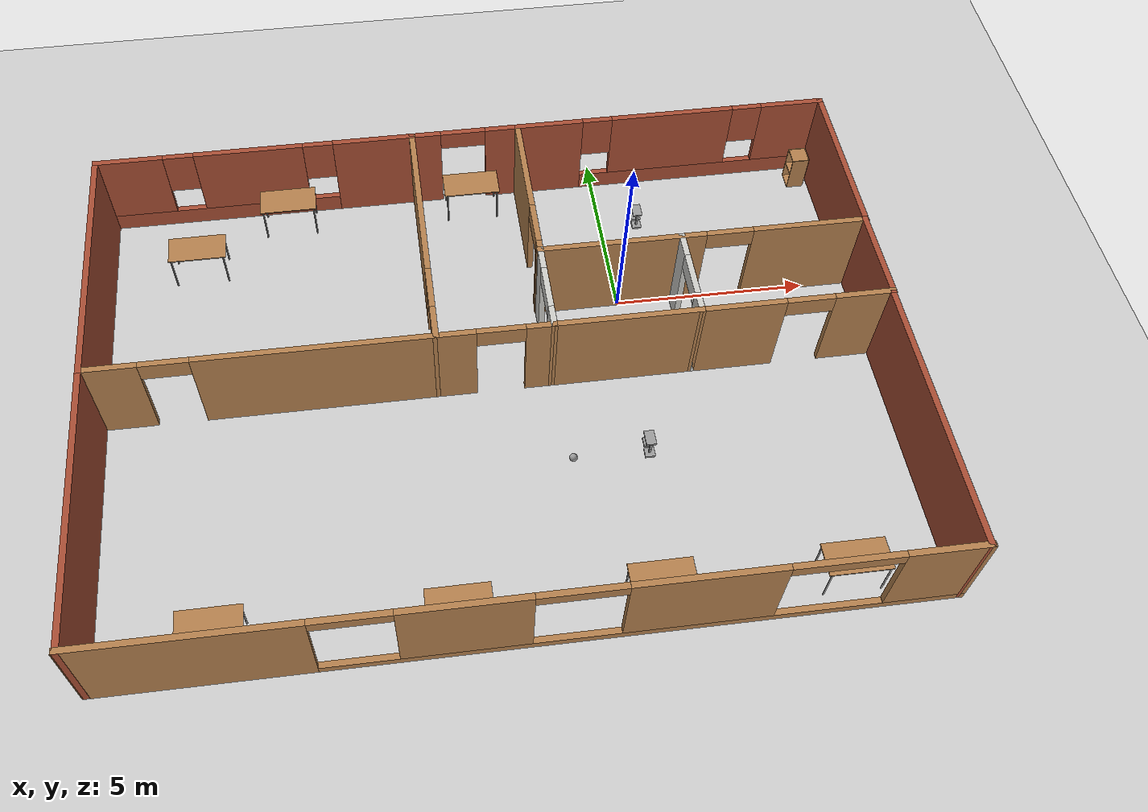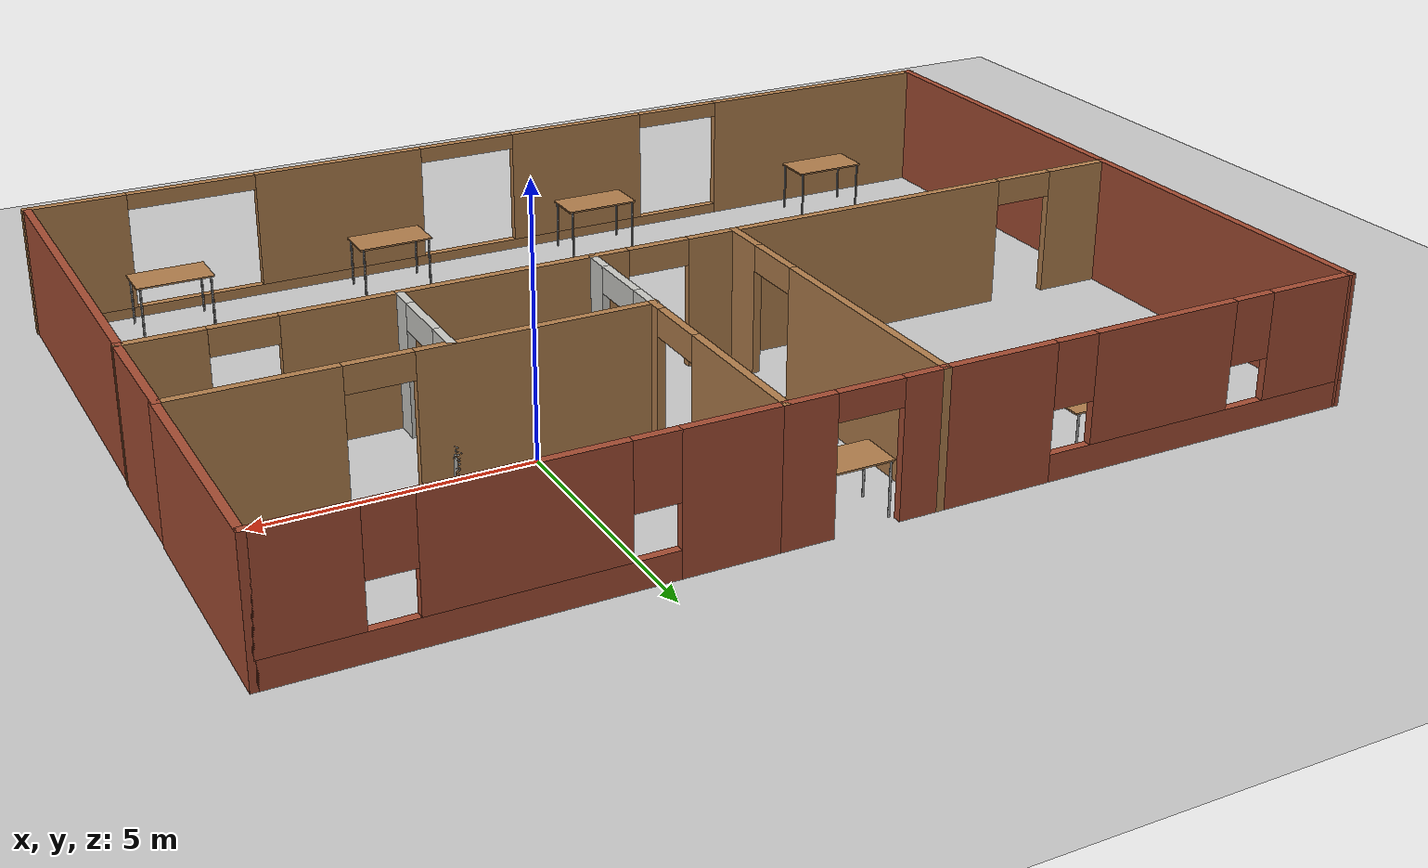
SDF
<sdf version="1.6">
 <world name="default">
  <plugin name="hello" filename="libhello.so"/>
  <light name="sun" type="directional">
   <pose>0 0 10 0 -0 0</pose>
   <diffuse>0.8 0.8 0.8 1</diffuse>
   <specular>0.2 0.2 0.2 1</specular>
   <attenuation>
    <range>1000</range>
    <constant>0.9</constant>
    <linear>0.01</linear>
    <quadratic>0.001</quadratic>
   </attenuation>
   <direction>-0.5 0.1 -0.9</direction>
  </light>
  <model name="ground_plane">
   <static>1</static>
   <link name="link">
    <collision name="collision">
     <geometry><plane><normal>0 0 1</normal><size>100 100</size></plane></geometry>
     <surface><friction><ode><mu>100</mu><mu2>50</mu2></ode></friction></surface>
    </collision>
    <visual name="visual">
     <cast_shadows>0</cast_shadows>
     <geometry><plane><normal>0 0 1</normal><size>100 100</size></plane></geometry>
     <material>
      <script><uri>file://media/materials/scripts/gazebo.material</uri><name>Gazebo/Grey</name></script>
     </material>
    </visual>
   </link>
  </model>
  <gravity>0 0 -9.8</gravity>
  <magnetic_field>6e-06 2.3e-05 -4.2e-05</magnetic_field>
  <atmosphere type="adiabatic"/>
  <physics name="default_physics" default="0" type="ode">
   <max_step_size>0.001</max_step_size>
   <real_time_factor>1</real_time_factor>
   <real_time_update_rate>1000</real_time_update_rate>
  </physics>
  <scene><ambient>0.4 0.4 0.4 1</ambient><background>0.7 0.7 0.7 1</background><shadows>1</shadows></scene>
  <spherical_coordinates>
   <surface_model>EARTH_WGS84</surface_model>
   <latitude_deg>0</latitude_deg>
   <longitude_deg>0</longitude_deg>
   <elevation>0</elevation>
   <heading_deg>0</heading_deg>
  </spherical_coordinates>
  <model name="table">
   <static>1</static>
   <link name="link">
    <collision name="surface">
     <pose>0 0 1 0 -0 0</pose>
     <geometry><box><size>1.5 0.8 0.03</size></box></geometry>
     <surface><friction><ode><mu>0.6</mu><mu2>0.6</mu2></ode></friction></surface>
    </collision>
    <visual name="visual1">
     <pose>0 0 1 0 -0 0</pose>
     <geometry><box><size>1.5 0.8 0.03</size></box></geometry>
     <material>
      <script><uri>file://media/materials/scripts/gazebo.material</uri><name>Gazebo/Wood</name></script>
     </material>
    </visual>
    <collision name="front_left_leg">
     <pose>0.68 0.38 0.5 0 -0 0</pose>
     <geometry><cylinder><radius>0.02</radius><length>1</length></cylinder></geometry>
    </collision>
    <visual name="front_left_leg">
     <pose>0.68 0.38 0.5 0 -0 0</pose>
     <geometry><cylinder><radius>0.02</radius><length>1</length></cylinder></geometry>
     <material>
      <script><uri>file://media/materials/scripts/gazebo.material</uri><name>Gazebo/Grey</name></script>
     </material>
    </visual>
    <collision name="front_right_leg">
     <pose>0.68 -0.38 0.5 0 -0 0</pose>
     <geometry><cylinder><radius>0.02</radius><length>1</length></cylinder></geometry>
    </collision>
    <visual name="front_right_leg">
     <pose>0.68 -0.38 0.5 0 -0 0</pose>
     <geometry><cylinder><radius>0.02</radius><length>1</length></cylinder></geometry>
     <material>
      <script><uri>file://media/materials/scripts/gazebo.material</uri><name>Gazebo/Grey</name></script>
     </material>
    </visual>
    <collision name="back_right_leg">
     <pose>-0.68 -0.38 0.5 0 -0 0</pose>
     <geometry><cylinder><radius>0.02</radius><length>1</length></cylinder></geometry>
    </collision>
    <visual name="back_right_leg">
     <pose>-0.68 -0.38 0.5 0 -0 0</pose>
     <geometry><cylinder><radius>0.02</radius><length>1</length></cylinder></geometry>
     <material>
      <script><uri>file://media/materials/scripts/gazebo.material</uri><name>Gazebo/Grey</name></script>
     </material>
    </visual>
    <collision name="back_left_leg">
     <pose>-0.68 0.38 0.5 0 -0 0</pose>
     <geometry><cylinder><radius>0.02</radius><length>1</length></cylinder></geometry>
    </collision>
    <visual name="back_left_leg">
     <pose>-0.68 0.38 0.5 0 -0 0</pose>
     <geometry><cylinder><radius>0.02</radius><length>1</length></cylinder></geometry>
     <material>
      <script><uri>file://media/materials/scripts/gazebo.material</uri><name>Gazebo/Grey</name></script>
     </material>
    </visual>
   </link>
   <pose>-10.5468 -8.35102 0 0 -0 0</pose>
  </model>
  <model name="Building">
   <pose>-3.56522 -2.42436 0 0 -0 0</pose>
   <link name="Wall_0">
    <pose>0.00123 6.80703 0 0 -0 0</pose>
    <visual name="Wall_0_Visual_0">
     <pose>-1.07927 0 1.25 0 -0 0</pose>
     <geometry><box><size>0.841459 0.15 2.5</size></box></geometry>
     <material>
      <script><uri>file://media/materials/scripts/gazebo.material</uri><name>Gazebo/Bricks</name></script>
      <ambient>1 1 1 1</ambient>
     </material>
     <meta><layer>0</layer></meta>
    </visual>
    <collision name="Wall_0_Collision_0">
     <geometry><box><size>0.841459 0.15 2.5</size></box></geometry>
     <pose>-1.07927 0 1.25 0 -0 0</pose>
    </collision>
    <visual name="Wall_0_Visual_1">
     <pose>1.02073 0 1.25 0 -0 0</pose>
     <geometry><box><size>0.958541 0.15 2.5</size></box></geometry>
     <material>
      <script><uri>file://media/materials/scripts/gazebo.material</uri><name>Gazebo/Bricks</name></script>
      <ambient>1 1 1 1</ambient>
     </material>
     <meta><layer>0</layer></meta>
    </visual>
    <collision name="Wall_0_Collision_1">
     <geometry><box><size>0.958541 0.15 2.5</size></box></geometry>
     <pose>1.02073 0 1.25 0 -0 0</pose>
    </collision>
    <visual name="Wall_0_Visual_2">
     <pose>-0.058541 0 2.25 0 -0 0</pose>
     <geometry><box><size>1.2 0.15 0.5</size></box></geometry>
     <material>
      <script><uri>file://media/materials/scripts/gazebo.material</uri><name>Gazebo/Bricks</name></script>
      <ambient>1 1 1 1</ambient>
     </material>
     <meta><layer>0</layer></meta>
    </visual>
    <collision name="Wall_0_Collision_2">
     <geometry><box><size>1.2 0.15 0.5</size></box></geometry>
     <pose>-0.058541 0 2.25 0 -0 0</pose>
    </collision>
   </link>
   <link name="Wall_1">
    <pose>1.42623 4.63203 0 0 0 -1.5708</pose>
    <visual name="Wall_1_Visual_0">
     <pose>-0.787008 0 1.25 0 -0 0</pose>
     <geometry><box><size>2.92598 0.15 2.5</size></box></geometry>
     <material>
      <script><uri>file://media/materials/scripts/gazebo.material</uri><name>Gazebo/Wood</name></script>
      <ambient>1 1 1 1</ambient>
     </material>
     <meta><layer>0</layer></meta>
    </visual>
    <collision name="Wall_1_Collision_0">
     <geometry><box><size>2.92598 0.15 2.5</size></box></geometry>
     <pose>-0.787008 0 1.25 0 -0 0</pose>
    </collision>
    <visual name="Wall_1_Visual_1">
     <pose>2.06299 0 1.25 0 -0 0</pose>
     <geometry><box><size>0.374017 0.15 2.5</size></box></geometry>
     <material>
      <script><uri>file://media/materials/scripts/gazebo.material</uri><name>Gazebo/Wood</name></script>
      <ambient>1 1 1 1</ambient>
     </material>
     <meta><layer>0</layer></meta>
    </visual>
    <collision name="Wall_1_Collision_1">
     <geometry><box><size>0.374017 0.15 2.5</size></box></geometry>
     <pose>2.06299 0 1.25 0 -0 0</pose>
    </collision>
    <visual name="Wall_1_Visual_2">
     <pose>1.27598 0 2.25 0 -0 0</pose>
     <geometry><box><size>1.2 0.15 0.5</size></box></geometry>
     <material>
      <script><uri>file://media/materials/scripts/gazebo.material</uri><name>Gazebo/Wood</name></script>
      <ambient>1 1 1 1</ambient>
     </material>
     <meta><layer>0</layer></meta>
    </visual>
    <collision name="Wall_1_Collision_2">
     <geometry><box><size>1.2 0.15 0.5</size></box></geometry>
     <pose>1.27598 0 2.25 0 -0 0</pose>
    </collision>
   </link>
   <link name="Wall_10">
    <pose>5.02623 1.28203 0 0 -0 1.5708</pose>
    <visual name="Wall_10_Visual_0">
     <pose>-0.954209 0 1.25 0 -0 0</pose>
     <geometry><box><size>0.591582 0.15 2.5</size></box></geometry>
     <material>
      <script><uri>file://media/materials/scripts/gazebo.material</uri><name>Gazebo/CeilingTiled</name></script>
      <ambient>1 1 1 1</ambient>
     </material>
     <meta><layer>0</layer></meta>
    </visual>
    <collision name="Wall_10_Collision_0">
     <geometry><box><size>0.591582 0.15 2.5</size></box></geometry>
     <pose>-0.954209 0 1.25 0 -0 0</pose>
    </collision>
    <visual name="Wall_10_Visual_1">
     <pose>0.895791 0 1.25 0 -0 0</pose>
     <geometry><box><size>0.708418 0.15 2.5</size></box></geometry>
     <material>
      <script><uri>file://media/materials/scripts/gazebo.material</uri><name>Gazebo/CeilingTiled</name></script>
      <ambient>1 1 1 1</ambient>
     </material>
     <meta><layer>0</layer></meta>
    </visual>
    <collision name="Wall_10_Collision_1">
     <geometry><box><size>0.708418 0.15 2.5</size></box></geometry>
     <pose>0.895791 0 1.25 0 -0 0</pose>
    </collision>
    <visual name="Wall_10_Visual_2">
     <pose>-0.058418 0 2.25 0 -0 0</pose>
     <geometry><box><size>1.2 0.15 0.5</size></box></geometry>
     <material>
      <script><uri>file://media/materials/scripts/gazebo.material</uri><name>Gazebo/CeilingTiled</name></script>
      <ambient>1 1 1 1</ambient>
     </material>
     <meta><layer>0</layer></meta>
    </visual>
    <collision name="Wall_10_Collision_2">
     <geometry><box><size>1.2 0.15 0.5</size></box></geometry>
     <pose>-0.058418 0 2.25 0 -0 0</pose>
    </collision>
   </link>
   <link name="Wall_14">
    <pose>-1.42237 3.45929 0 0 0 -1.57038</pose>
    <visual name="Wall_14_Visual_0">
     <pose>-1.07421 0 1.25 0 -0 0</pose>
     <geometry><box><size>4.69716 0.15 2.5</size></box></geometry>
     <material>
      <script><uri>file://media/materials/scripts/gazebo.material</uri><name>Gazebo/Wood</name></script>
      <ambient>1 1 1 1</ambient>
     </material>
     <meta><layer>0</layer></meta>
    </visual>
    <collision name="Wall_14_Collision_0">
     <geometry><box><size>4.69716 0.15 2.5</size></box></geometry>
     <pose>-1.07421 0 1.25 0 -0 0</pose>
    </collision>
    <visual name="Wall_14_Visual_1">
     <pose>2.94858 0 1.25 0 -0 0</pose>
     <geometry><box><size>0.94843 0.15 2.5</size></box></geometry>
     <material>
      <script><uri>file://media/materials/scripts/gazebo.material</uri><name>Gazebo/Wood</name></script>
      <ambient>1 1 1 1</ambient>
     </material>
     <meta><layer>0</layer></meta>
    </visual>
    <collision name="Wall_14_Collision_1">
     <geometry><box><size>0.94843 0.15 2.5</size></box></geometry>
     <pose>2.94858 0 1.25 0 -0 0</pose>
    </collision>
    <visual name="Wall_14_Visual_2">
     <pose>1.87437 0 2.25 0 -0 0</pose>
     <geometry><box><size>1.2 0.15 0.5</size></box></geometry>
     <material>
      <script><uri>file://media/materials/scripts/gazebo.material</uri><name>Gazebo/Wood</name></script>
      <ambient>1 1 1 1</ambient>
     </material>
     <meta><layer>0</layer></meta>
    </visual>
    <collision name="Wall_14_Collision_2">
     <geometry><box><size>1.2 0.15 0.5</size></box></geometry>
     <pose>1.87437 0 2.25 0 -0 0</pose>
    </collision>
   </link>
   <link name="Wall_15">
    <pose>0.002634 0.109288 0 0 0 -0.001586</pose>
    <visual name="Wall_15_Visual_0">
     <pose>-0.976905 0 1.25 0 -0 0</pose>
     <geometry><box><size>1.04339 0.15 2.5</size></box></geometry>
     <material>
      <script><uri>file://media/materials/scripts/gazebo.material</uri><name>Gazebo/Wood</name></script>
      <ambient>1 1 1 1</ambient>
     </material>
     <meta><layer>0</layer></meta>
    </visual>
    <collision name="Wall_15_Collision_0">
     <geometry><box><size>1.04339 0.15 2.5</size></box></geometry>
     <pose>-0.976905 0 1.25 0 -0 0</pose>
    </collision>
    <visual name="Wall_15_Visual_1">
     <pose>1.12169 0 1.25 0 -0 0</pose>
     <geometry><box><size>0.753809 0.15 2.5</size></box></geometry>
     <material>
      <script><uri>file://media/materials/scripts/gazebo.material</uri><name>Gazebo/Wood</name></script>
      <ambient>1 1 1 1</ambient>
     </material>
     <meta><layer>0</layer></meta>
    </visual>
    <collision name="Wall_15_Collision_1">
     <geometry><box><size>0.753809 0.15 2.5</size></box></geometry>
     <pose>1.12169 0 1.25 0 -0 0</pose>
    </collision>
    <visual name="Wall_15_Visual_2">
     <pose>0.144788 0 2.25 0 -0 0</pose>
     <geometry><box><size>1.2 0.15 0.5</size></box></geometry>
     <material>
      <script><uri>file://media/materials/scripts/gazebo.material</uri><name>Gazebo/Wood</name></script>
      <ambient>1 1 1 1</ambient>
     </material>
     <meta><layer>0</layer></meta>
    </visual>
    <collision name="Wall_15_Collision_2">
     <geometry><box><size>1.2 0.15 0.5</size></box></geometry>
     <pose>0.144788 0 2.25 0 -0 0</pose>
    </collision>
   </link>
   <link name="Wall_17">
    <pose>-5.59877 6.80703 0 0 -0 3.14159</pose>
    <visual name="Wall_17_Visual_0">
     <pose>-3.15253 0 1.25 0 -0 0</pose>
     <geometry><box><size>2.19494 0.15 2.5</size></box></geometry>
     <material>
      <script><uri>file://media/materials/scripts/gazebo.material</uri><name>Gazebo/Bricks</name></script>
      <ambient>1 1 1 1</ambient>
     </material>
     <meta><layer>0</layer></meta>
    </visual>
    <collision name="Wall_17_Collision_0">
     <geometry><box><size>2.19494 0.15 2.5</size></box></geometry>
     <pose>-3.15253 0 1.25 0 -0 0</pose>
    </collision>
    <visual name="Wall_17_Visual_1">
     <pose>1.09747 0 0.25 0 -0 0</pose>
     <geometry><box><size>6.30506 0.15 0.5</size></box></geometry>
     <material>
      <script><uri>file://media/materials/scripts/gazebo.material</uri><name>Gazebo/Bricks</name></script>
      <ambient>1 1 1 1</ambient>
     </material>
     <meta><layer>0</layer></meta>
    </visual>
    <collision name="Wall_17_Collision_1">
     <geometry><box><size>6.30506 0.15 0.5</size></box></geometry>
     <pose>1.09747 0 0.25 0 -0 0</pose>
    </collision>
    <visual name="Wall_17_Visual_2">
     <pose>0.184146 0 1.5 0 -0 0</pose>
     <geometry><box><size>2.8784 0.15 2</size></box></geometry>
     <material>
      <script><uri>file://media/materials/scripts/gazebo.material</uri><name>Gazebo/Bricks</name></script>
      <ambient>1 1 1 1</ambient>
     </material>
     <meta><layer>0</layer></meta>
    </visual>
    <collision name="Wall_17_Collision_2">
     <geometry><box><size>2.8784 0.15 2</size></box></geometry>
     <pose>0.184146 0 1.5 0 -0 0</pose>
    </collision>
    <visual name="Wall_17_Visual_3">
     <pose>3.33667 0 1.5 0 -0 0</pose>
     <geometry><box><size>1.82665 0.15 2</size></box></geometry>
     <material>
      <script><uri>file://media/materials/scripts/gazebo.material</uri><name>Gazebo/Bricks</name></script>
      <ambient>1 1 1 1</ambient>
     </material>
     <meta><layer>0</layer></meta>
    </visual>
    <collision name="Wall_17_Collision_3">
     <geometry><box><size>1.82665 0.15 2</size></box></geometry>
     <pose>3.33667 0 1.5 0 -0 0</pose>
    </collision>
    <visual name="Wall_17_Visual_4">
     <pose>-1.65506 0 1.9 0 -0 0</pose>
     <geometry><box><size>0.8 0.15 1.2</size></box></geometry>
     <material>
      <script><uri>file://media/materials/scripts/gazebo.material</uri><name>Gazebo/Bricks</name></script>
      <ambient>1 1 1 1</ambient>
     </material>
     <meta><layer>0</layer></meta>
    </visual>
    <collision name="Wall_17_Collision_4">
     <geometry><box><size>0.8 0.15 1.2</size></box></geometry>
     <pose>-1.65506 0 1.9 0 -0 0</pose>
    </collision>
    <visual name="Wall_17_Visual_5">
     <pose>2.02335 0 1.9 0 -0 0</pose>
     <geometry><box><size>0.8 0.15 1.2</size></box></geometry>
     <material>
      <script><uri>file://media/materials/scripts/gazebo.material</uri><name>Gazebo/Bricks</name></script>
      <ambient>1 1 1 1</ambient>
     </material>
     <meta><layer>0</layer></meta>
    </visual>
    <collision name="Wall_17_Collision_5">
     <geometry><box><size>0.8 0.15 1.2</size></box></geometry>
     <pose>2.02335 0 1.9 0 -0 0</pose>
    </collision>
   </link>
   <link name="Wall_18">
    <collision name="Wall_18_Collision">
     <geometry><box><size>6.84549 0.15 2.5</size></box></geometry>
     <pose>0 0 1.25 0 -0 0</pose>
    </collision>
    <visual name="Wall_18_Visual">
     <pose>0 0 1.25 0 -0 0</pose>
     <geometry><box><size>6.84549 0.15 2.5</size></box></geometry>
     <material>
      <script><uri>file://media/materials/scripts/gazebo.material</uri><name>Gazebo/Bricks</name></script>
      <ambient>1 1 1 1</ambient>
     </material>
     <meta><layer>0</layer></meta>
    </visual>
    <pose>-9.77237 3.45929 0 0 0 -1.57038</pose>
   </link>
   <link name="Wall_19">
    <pose>-5.59596 0.111546 0 0 -0 0</pose>
    <visual name="Wall_19_Visual_0">
     <pose>-3.53632 0 1.25 0 -0 0</pose>
     <geometry><box><size>1.42737 0.15 2.5</size></box></geometry>
     <material>
      <script><uri>file://media/materials/scripts/gazebo.material</uri><name>Gazebo/Wood</name></script>
      <ambient>1 1 1 1</ambient>
     </material>
     <meta><layer>0</layer></meta>
    </visual>
    <collision name="Wall_19_Collision_0">
     <geometry><box><size>1.42737 0.15 2.5</size></box></geometry>
     <pose>-3.53632 0 1.25 0 -0 0</pose>
    </collision>
    <visual name="Wall_19_Visual_1">
     <pose>1.31368 0 1.25 0 -0 0</pose>
     <geometry><box><size>5.87263 0.15 2.5</size></box></geometry>
     <material>
      <script><uri>file://media/materials/scripts/gazebo.material</uri><name>Gazebo/Wood</name></script>
      <ambient>1 1 1 1</ambient>
     </material>
     <meta><layer>0</layer></meta>
    </visual>
    <collision name="Wall_19_Collision_1">
     <geometry><box><size>5.87263 0.15 2.5</size></box></geometry>
     <pose>1.31368 0 1.25 0 -0 0</pose>
    </collision>
    <visual name="Wall_19_Visual_2">
     <pose>-2.22263 0 2.25 0 -0 0</pose>
     <geometry><box><size>1.2 0.15 0.5</size></box></geometry>
     <material>
      <script><uri>file://media/materials/scripts/gazebo.material</uri><name>Gazebo/Wood</name></script>
      <ambient>1 1 1 1</ambient>
     </material>
     <meta><layer>0</layer></meta>
    </visual>
    <collision name="Wall_19_Collision_2">
     <geometry><box><size>1.2 0.15 0.5</size></box></geometry>
     <pose>-2.22263 0 2.25 0 -0 0</pose>
    </collision>
   </link>
   <link name="Wall_21">
    <collision name="Wall_21_Collision">
     <geometry><box><size>7.06897 0.15 2.5</size></box></geometry>
     <pose>0 0 1.25 0 -0 0</pose>
    </collision>
    <visual name="Wall_21_Visual">
     <pose>0 0 1.25 0 -0 0</pose>
     <geometry><box><size>7.06897 0.15 2.5</size></box></geometry>
     <material>
      <script><uri>file://media/materials/scripts/gazebo.material</uri><name>Gazebo/Bricks</name></script>
      <ambient>1 1 1 1</ambient>
     </material>
     <meta><layer>0</layer></meta>
    </visual>
    <pose>-9.76503 -3.34751 0 0 0 -1.56908</pose>
   </link>
   <link name="Wall_22">
    <pose>0 -6.80657 0 0 -0 0</pose>
    <visual name="Wall_22_Visual_0">
     <pose>-7.30329 0 1.25 0 -0 0</pose>
     <geometry><box><size>5.11 0.15 2.5</size></box></geometry>
     <material>
      <script><uri>file://media/materials/scripts/gazebo.material</uri><name>Gazebo/Wood</name></script>
      <ambient>1 1 1 1</ambient>
     </material>
     <meta><layer>0</layer></meta>
    </visual>
    <collision name="Wall_22_Collision_0">
     <geometry><box><size>5.11 0.15 2.5</size></box></geometry>
     <pose>-7.30329 0 1.25 0 -0 0</pose>
    </collision>
    <visual name="Wall_22_Visual_1">
     <pose>2.555 0 0.1 0 -0 0</pose>
     <geometry><box><size>14.6066 0.15 0.2</size></box></geometry>
     <material>
      <script><uri>file://media/materials/scripts/gazebo.material</uri><name>Gazebo/Wood</name></script>
      <ambient>1 1 1 1</ambient>
     </material>
     <meta><layer>0</layer></meta>
    </visual>
    <collision name="Wall_22_Collision_1">
     <geometry><box><size>14.6066 0.15 0.2</size></box></geometry>
     <pose>2.555 0 0.1 0 -0 0</pose>
    </collision>
    <visual name="Wall_22_Visual_2">
     <pose>-1.47869 0 1.35 0 -0 0</pose>
     <geometry><box><size>2.93921 0.15 2.3</size></box></geometry>
     <material>
      <script><uri>file://media/materials/scripts/gazebo.material</uri><name>Gazebo/Wood</name></script>
      <ambient>1 1 1 1</ambient>
     </material>
     <meta><layer>0</layer></meta>
    </visual>
    <collision name="Wall_22_Collision_2">
     <geometry><box><size>2.93921 0.15 2.3</size></box></geometry>
     <pose>-1.47869 0 1.35 0 -0 0</pose>
    </collision>
    <visual name="Wall_22_Visual_3">
     <pose>3.70769 0 1.35 0 -0 0</pose>
     <geometry><box><size>3.43355 0.15 2.3</size></box></geometry>
     <material>
      <script><uri>file://media/materials/scripts/gazebo.material</uri><name>Gazebo/Wood</name></script>
      <ambient>1 1 1 1</ambient>
     </material>
     <meta><layer>0</layer></meta>
    </visual>
    <collision name="Wall_22_Collision_3">
     <geometry><box><size>3.43355 0.15 2.3</size></box></geometry>
     <pose>3.70769 0 1.35 0 -0 0</pose>
    </collision>
    <visual name="Wall_22_Visual_4">
     <pose>8.89138 0 1.35 0 -0 0</pose>
     <geometry><box><size>1.93382 0.15 2.3</size></box></geometry>
     <material>
      <script><uri>file://media/materials/scripts/gazebo.material</uri><name>Gazebo/Wood</name></script>
      <ambient>1 1 1 1</ambient>
     </material>
     <meta><layer>0</layer></meta>
    </visual>
    <collision name="Wall_22_Collision_4">
     <geometry><box><size>1.93382 0.15 2.3</size></box></geometry>
     <pose>8.89138 0 1.35 0 -0 0</pose>
    </collision>
    <visual name="Wall_22_Visual_5">
     <pose>-3.84829 0 2.35 0 -0 0</pose>
     <geometry><box><size>1.8 0.15 0.3</size></box></geometry>
     <material>
      <script><uri>file://media/materials/scripts/gazebo.material</uri><name>Gazebo/Wood</name></script>
      <ambient>1 1 1 1</ambient>
     </material>
     <meta><layer>0</layer></meta>
    </visual>
    <collision name="Wall_22_Collision_5">
     <geometry><box><size>1.8 0.15 0.3</size></box></geometry>
     <pose>-3.84829 0 2.35 0 -0 0</pose>
    </collision>
    <visual name="Wall_22_Visual_6">
     <pose>0.990915 0 2.35 0 -0 0</pose>
     <geometry><box><size>2 0.15 0.3</size></box></geometry>
     <material>
      <script><uri>file://media/materials/scripts/gazebo.material</uri><name>Gazebo/Wood</name></script>
      <ambient>1 1 1 1</ambient>
     </material>
     <meta><layer>0</layer></meta>
    </visual>
    <collision name="Wall_22_Collision_6">
     <geometry><box><size>2 0.15 0.3</size></box></geometry>
     <pose>0.990915 0 2.35 0 -0 0</pose>
    </collision>
    <visual name="Wall_22_Visual_7">
     <pose>6.67447 0 2.35 0 -0 0</pose>
     <geometry><box><size>2.5 0.15 0.3</size></box></geometry>
     <material>
      <script><uri>file://media/materials/scripts/gazebo.material</uri><name>Gazebo/Wood</name></script>
      <ambient>1 1 1 1</ambient>
     </material>
     <meta><layer>0</layer></meta>
    </visual>
    <collision name="Wall_22_Collision_7">
     <geometry><box><size>2.5 0.15 0.3</size></box></geometry>
     <pose>6.67447 0 2.35 0 -0 0</pose>
    </collision>
   </link>
   <link name="Wall_23">
    <collision name="Wall_23_Collision">
     <geometry><box><size>7.06812 0.15 2.5</size></box></geometry>
     <pose>0 0 1.25 0 -0 0</pose>
    </collision>
    <visual name="Wall_23_Visual">
     <pose>0 0 1.25 0 -0 0</pose>
     <geometry><box><size>7.06812 0.15 2.5</size></box></geometry>
     <material>
      <script><uri>file://media/materials/scripts/gazebo.material</uri><name>Gazebo/Bricks</name></script>
      <ambient>1 1 1 1</ambient>
     </material>
     <meta><layer>0</layer></meta>
    </visual>
    <pose>9.75331 -3.34751 0 0 -0 1.57251</pose>
   </link>
   <link name="Wall_24">
    <pose>7.39883 0.109288 0 0 0 -3.14064</pose>
    <visual name="Wall_24_Visual_0">
     <pose>-1.68708 0 1.25 0 -0 0</pose>
     <geometry><box><size>1.52105 0.15 2.5</size></box></geometry>
     <material>
      <script><uri>file://media/materials/scripts/gazebo.material</uri><name>Gazebo/Wood</name></script>
      <ambient>1 1 1 1</ambient>
     </material>
     <meta><layer>0</layer></meta>
    </visual>
    <collision name="Wall_24_Collision_0">
     <geometry><box><size>1.52105 0.15 2.5</size></box></geometry>
     <pose>-1.68708 0 1.25 0 -0 0</pose>
    </collision>
    <visual name="Wall_24_Visual_1">
     <pose>1.36053 0 1.25 0 -0 0</pose>
     <geometry><box><size>2.17416 0.15 2.5</size></box></geometry>
     <material>
      <script><uri>file://media/materials/scripts/gazebo.material</uri><name>Gazebo/Wood</name></script>
      <ambient>1 1 1 1</ambient>
     </material>
     <meta><layer>0</layer></meta>
    </visual>
    <collision name="Wall_24_Collision_1">
     <geometry><box><size>2.17416 0.15 2.5</size></box></geometry>
     <pose>1.36053 0 1.25 0 -0 0</pose>
    </collision>
    <visual name="Wall_24_Visual_2">
     <pose>-0.326552 0 2.25 0 -0 0</pose>
     <geometry><box><size>1.2 0.15 0.5</size></box></geometry>
     <material>
      <script><uri>file://media/materials/scripts/gazebo.material</uri><name>Gazebo/Wood</name></script>
      <ambient>1 1 1 1</ambient>
     </material>
     <meta><layer>0</layer></meta>
    </visual>
    <collision name="Wall_24_Collision_2">
     <geometry><box><size>1.2 0.15 0.5</size></box></geometry>
     <pose>-0.326552 0 2.25 0 -0 0</pose>
    </collision>
   </link>
   <link name="Wall_26">
    <collision name="Wall_26_Collision">
     <geometry><box><size>2.49552 0.15 2.5</size></box></geometry>
     <pose>0 0 1.25 0 -0 0</pose>
    </collision>
    <visual name="Wall_26_Visual">
     <pose>0 0 1.25 0 -0 0</pose>
     <geometry><box><size>2.49552 0.15 2.5</size></box></geometry>
     <material>
      <script><uri>file://media/materials/scripts/gazebo.material</uri><name>Gazebo/Bricks</name></script>
      <ambient>1 1 1 1</ambient>
     </material>
     <meta><layer>0</layer></meta>
    </visual>
    <pose>9.76487 1.28429 0 0 0 -1.56519</pose>
   </link>
   <link name="Wall_3">
    <pose>5.60123 6.80703 0 0 -0 0</pose>
    <visual name="Wall_3_Visual_0">
     <pose>-3.32227 0 1.25 0 -0 0</pose>
     <geometry><box><size>1.85546 0.15 2.5</size></box></geometry>
     <material>
      <script><uri>file://media/materials/scripts/gazebo.material</uri><name>Gazebo/Bricks</name></script>
      <ambient>1 1 1 1</ambient>
     </material>
     <meta><layer>0</layer></meta>
    </visual>
    <collision name="Wall_3_Collision_0">
     <geometry><box><size>1.85546 0.15 2.5</size></box></geometry>
     <pose>-3.32227 0 1.25 0 -0 0</pose>
    </collision>
    <visual name="Wall_3_Visual_1">
     <pose>0.927733 0 0.25 0 -0 0</pose>
     <geometry><box><size>6.64454 0.15 0.5</size></box></geometry>
     <material>
      <script><uri>file://media/materials/scripts/gazebo.material</uri><name>Gazebo/Bricks</name></script>
      <ambient>1 1 1 1</ambient>
     </material>
     <meta><layer>0</layer></meta>
    </visual>
    <collision name="Wall_3_Collision_1">
     <geometry><box><size>6.64454 0.15 0.5</size></box></geometry>
     <pose>0.927733 0 0.25 0 -0 0</pose>
    </collision>
    <visual name="Wall_3_Visual_2">
     <pose>0.065925 0 1.5 0 -0 0</pose>
     <geometry><box><size>3.32092 0.15 2</size></box></geometry>
     <material>
      <script><uri>file://media/materials/scripts/gazebo.material</uri><name>Gazebo/Bricks</name></script>
      <ambient>1 1 1 1</ambient>
     </material>
     <meta><layer>0</layer></meta>
    </visual>
    <collision name="Wall_3_Collision_2">
     <geometry><box><size>3.32092 0.15 2</size></box></geometry>
     <pose>0.065925 0 1.5 0 -0 0</pose>
    </collision>
    <visual name="Wall_3_Visual_3">
     <pose>3.38819 0 1.5 0 -0 0</pose>
     <geometry><box><size>1.72362 0.15 2</size></box></geometry>
     <material>
      <script><uri>file://media/materials/scripts/gazebo.material</uri><name>Gazebo/Bricks</name></script>
      <ambient>1 1 1 1</ambient>
     </material>
     <meta><layer>0</layer></meta>
    </visual>
    <collision name="Wall_3_Collision_3">
     <geometry><box><size>1.72362 0.15 2</size></box></geometry>
     <pose>3.38819 0 1.5 0 -0 0</pose>
    </collision>
    <visual name="Wall_3_Visual_4">
     <pose>-1.99453 0 1.9 0 -0 0</pose>
     <geometry><box><size>0.8 0.15 1.2</size></box></geometry>
     <material>
      <script><uri>file://media/materials/scripts/gazebo.material</uri><name>Gazebo/Bricks</name></script>
      <ambient>1 1 1 1</ambient>
     </material>
     <meta><layer>0</layer></meta>
    </visual>
    <collision name="Wall_3_Collision_4">
     <geometry><box><size>0.8 0.15 1.2</size></box></geometry>
     <pose>-1.99453 0 1.9 0 -0 0</pose>
    </collision>
    <visual name="Wall_3_Visual_5">
     <pose>2.12638 0 1.9 0 -0 0</pose>
     <geometry><box><size>0.8 0.15 1.2</size></box></geometry>
     <material>
      <script><uri>file://media/materials/scripts/gazebo.material</uri><name>Gazebo/Bricks</name></script>
      <ambient>1 1 1 1</ambient>
     </material>
     <meta><layer>0</layer></meta>
    </visual>
    <collision name="Wall_3_Collision_5">
     <geometry><box><size>0.8 0.15 1.2</size></box></geometry>
     <pose>2.12638 0 1.9 0 -0 0</pose>
    </collision>
   </link>
   <link name="Wall_4">
    <collision name="Wall_4_Collision">
     <geometry><box><size>4.5 0.15 2.5</size></box></geometry>
     <pose>0 0 1.25 0 -0 0</pose>
    </collision>
    <visual name="Wall_4_Visual">
     <pose>0 0 1.25 0 -0 0</pose>
     <geometry><box><size>4.5 0.15 2.5</size></box></geometry>
     <material>
      <script><uri>file://media/materials/scripts/gazebo.material</uri><name>Gazebo/Bricks</name></script>
      <ambient>1 1 1 1</ambient>
     </material>
     <meta><layer>0</layer></meta>
    </visual>
    <pose>9.77623 4.63203 0 0 0 -1.5708</pose>
   </link>
   <link name="Wall_5">
    <pose>5.58329 2.45703 0 0 -0 3.14159</pose>
    <visual name="Wall_5_Visual_0">
     <pose>-2.76355 0 1.25 0 -0 0</pose>
     <geometry><box><size>2.9729 0.15 2.5</size></box></geometry>
     <material>
      <script><uri>file://media/materials/scripts/gazebo.material</uri><name>Gazebo/Wood</name></script>
      <ambient>1 1 1 1</ambient>
     </material>
     <meta><layer>0</layer></meta>
    </visual>
    <collision name="Wall_5_Collision_0">
     <geometry><box><size>2.9729 0.15 2.5</size></box></geometry>
     <pose>-2.76355 0 1.25 0 -0 0</pose>
    </collision>
    <visual name="Wall_5_Visual_1">
     <pose>2.08645 0 1.25 0 -0 0</pose>
     <geometry><box><size>4.3271 0.15 2.5</size></box></geometry>
     <material>
      <script><uri>file://media/materials/scripts/gazebo.material</uri><name>Gazebo/Wood</name></script>
      <ambient>1 1 1 1</ambient>
     </material>
     <meta><layer>0</layer></meta>
    </visual>
    <collision name="Wall_5_Collision_1">
     <geometry><box><size>4.3271 0.15 2.5</size></box></geometry>
     <pose>2.08645 0 1.25 0 -0 0</pose>
    </collision>
    <visual name="Wall_5_Visual_2">
     <pose>-0.677101 0 2.25 0 -0 0</pose>
     <geometry><box><size>1.2 0.15 0.5</size></box></geometry>
     <material>
      <script><uri>file://media/materials/scripts/gazebo.material</uri><name>Gazebo/Wood</name></script>
      <ambient>1 1 1 1</ambient>
     </material>
     <meta><layer>0</layer></meta>
    </visual>
    <collision name="Wall_5_Collision_2">
     <geometry><box><size>1.2 0.15 0.5</size></box></geometry>
     <pose>-0.677101 0 2.25 0 -0 0</pose>
    </collision>
   </link>
   <link name="Wall_8">
    <pose>1.42623 1.28203 0 0 0 -1.5708</pose>
    <visual name="Wall_8_Visual_0">
     <pose>-0.910439 0 1.25 0 -0 0</pose>
     <geometry><box><size>0.679123 0.15 2.5</size></box></geometry>
     <material>
      <script><uri>file://media/materials/scripts/gazebo.material</uri><name>Gazebo/CeilingTiled</name></script>
      <ambient>1 1 1 1</ambient>
     </material>
     <meta><layer>0</layer></meta>
    </visual>
    <collision name="Wall_8_Collision_0">
     <geometry><box><size>0.679123 0.15 2.5</size></box></geometry>
     <pose>-0.910439 0 1.25 0 -0 0</pose>
    </collision>
    <visual name="Wall_8_Visual_1">
     <pose>0.939561 0 1.25 0 -0 0</pose>
     <geometry><box><size>0.620877 0.15 2.5</size></box></geometry>
     <material>
      <script><uri>file://media/materials/scripts/gazebo.material</uri><name>Gazebo/CeilingTiled</name></script>
      <ambient>1 1 1 1</ambient>
     </material>
     <meta><layer>0</layer></meta>
    </visual>
    <collision name="Wall_8_Collision_1">
     <geometry><box><size>0.620877 0.15 2.5</size></box></geometry>
     <pose>0.939561 0 1.25 0 -0 0</pose>
    </collision>
    <visual name="Wall_8_Visual_2">
     <pose>0.029123 0 2.25 0 -0 0</pose>
     <geometry><box><size>1.2 0.15 0.5</size></box></geometry>
     <material>
      <script><uri>file://media/materials/scripts/gazebo.material</uri><name>Gazebo/CeilingTiled</name></script>
      <ambient>1 1 1 1</ambient>
     </material>
     <meta><layer>0</layer></meta>
    </visual>
    <collision name="Wall_8_Collision_2">
     <geometry><box><size>1.2 0.15 0.5</size></box></geometry>
     <pose>0.029123 0 2.25 0 -0 0</pose>
    </collision>
   </link>
   <link name="Wall_9">
    <collision name="Wall_9_Collision">
     <geometry><box><size>3.75 0.15 2.5</size></box></geometry>
     <pose>0 0 1.25 0 -0 0</pose>
    </collision>
    <visual name="Wall_9_Visual">
     <pose>0 0 1.25 0 -0 0</pose>
     <geometry><box><size>3.75 0.15 2.5</size></box></geometry>
     <material>
      <script><uri>file://media/materials/scripts/gazebo.material</uri><name>Gazebo/Wood</name></script>
      <ambient>1 1 1 1</ambient>
     </material>
     <meta><layer>0</layer></meta>
    </visual>
    <pose>3.22623 0.10703 0 0 -0 0</pose>
   </link>
   <static>1</static>
  </model>
  <model name="table_clone">
   <static>1</static>
   <link name="link">
    <collision name="surface">
     <pose>0 0 1 0 -0 0</pose>
     <geometry><box><size>1.5 0.8 0.03</size></box></geometry>
     <surface><friction><ode><mu>0.6</mu><mu2>0.6</mu2></ode></friction></surface>
    </collision>
    <visual name="visual1">
     <pose>0 0 1 0 -0 0</pose>
     <geometry><box><size>1.5 0.8 0.03</size></box></geometry>
     <material>
      <script><uri>file://media/materials/scripts/gazebo.material</uri><name>Gazebo/Wood</name></script>
     </material>
    </visual>
    <collision name="front_left_leg">
     <pose>0.68 0.38 0.5 0 -0 0</pose>
     <geometry><cylinder><radius>0.02</radius><length>1</length></cylinder></geometry>
    </collision>
    <visual name="front_left_leg">
     <pose>0.68 0.38 0.5 0 -0 0</pose>
     <geometry><cylinder><radius>0.02</radius><length>1</length></cylinder></geometry>
     <material>
      <script><uri>file://media/materials/scripts/gazebo.material</uri><name>Gazebo/Grey</name></script>
     </material>
    </visual>
    <collision name="front_right_leg">
     <pose>0.68 -0.38 0.5 0 -0 0</pose>
     <geometry><cylinder><radius>0.02</radius><length>1</length></cylinder></geometry>
    </collision>
    <visual name="front_right_leg">
     <pose>0.68 -0.38 0.5 0 -0 0</pose>
     <geometry><cylinder><radius>0.02</radius><length>1</length></cylinder></geometry>
     <material>
      <script><uri>file://media/materials/scripts/gazebo.material</uri><name>Gazebo/Grey</name></script>
     </material>
    </visual>
    <collision name="back_right_leg">
     <pose>-0.68 -0.38 0.5 0 -0 0</pose>
     <geometry><cylinder><radius>0.02</radius><length>1</length></cylinder></geometry>
    </collision>
    <visual name="back_right_leg">
     <pose>-0.68 -0.38 0.5 0 -0 0</pose>
     <geometry><cylinder><radius>0.02</radius><length>1</length></cylinder></geometry>
     <material>
      <script><uri>file://media/materials/scripts/gazebo.material</uri><name>Gazebo/Grey</name></script>
     </material>
    </visual>
    <collision name="back_left_leg">
     <pose>-0.68 0.38 0.5 0 -0 0</pose>
     <geometry><cylinder><radius>0.02</radius><length>1</length></cylinder></geometry>
    </collision>
    <visual name="back_left_leg">
     <pose>-0.68 0.38 0.5 0 -0 0</pose>
     <geometry><cylinder><radius>0.02</radius><length>1</length></cylinder></geometry>
     <material>
      <script><uri>file://media/materials/scripts/gazebo.material</uri><name>Gazebo/Grey</name></script>
     </material>
    </visual>
   </link>
   <pose>-10.936 2.42939 0 0 -0 0</pose>
  </model>
  <model name="table_clone_0">
   <static>1</static>
   <link name="link">
    <collision name="surface">
     <pose>0 0 1 0 -0 0</pose>
     <geometry><box><size>1.5 0.8 0.03</size></box></geometry>
     <surface><friction><ode><mu>0.6</mu><mu2>0.6</mu2></ode></friction></surface>
    </collision>
    <visual name="visual1">
     <pose>0 0 1 0 -0 0</pose>
     <geometry><box><size>1.5 0.8 0.03</size></box></geometry>
     <material>
      <script><uri>file://media/materials/scripts/gazebo.material</uri><name>Gazebo/Wood</name></script>
     </material>
    </visual>
    <collision name="front_left_leg">
     <pose>0.68 0.38 0.5 0 -0 0</pose>
     <geometry><cylinder><radius>0.02</radius><length>1</length></cylinder></geometry>
    </collision>
    <visual name="front_left_leg">
     <pose>0.68 0.38 0.5 0 -0 0</pose>
     <geometry><cylinder><radius>0.02</radius><length>1</length></cylinder></geometry>
     <material>
      <script><uri>file://media/materials/scripts/gazebo.material</uri><name>Gazebo/Grey</name></script>
     </material>
    </visual>
    <collision name="front_right_leg">
     <pose>0.68 -0.38 0.5 0 -0 0</pose>
     <geometry><cylinder><radius>0.02</radius><length>1</length></cylinder></geometry>
    </collision>
    <visual name="front_right_leg">
     <pose>0.68 -0.38 0.5 0 -0 0</pose>
     <geometry><cylinder><radius>0.02</radius><length>1</length></cylinder></geometry>
     <material>
      <script><uri>file://media/materials/scripts/gazebo.material</uri><name>Gazebo/Grey</name></script>
     </material>
    </visual>
    <collision name="back_right_leg">
     <pose>-0.68 -0.38 0.5 0 -0 0</pose>
     <geometry><cylinder><radius>0.02</radius><length>1</length></cylinder></geometry>
    </collision>
    <visual name="back_right_leg">
     <pose>-0.68 -0.38 0.5 0 -0 0</pose>
     <geometry><cylinder><radius>0.02</radius><length>1</length></cylinder></geometry>
     <material>
      <script><uri>file://media/materials/scripts/gazebo.material</uri><name>Gazebo/Grey</name></script>
     </material>
    </visual>
    <collision name="back_left_leg">
     <pose>-0.68 0.38 0.5 0 -0 0</pose>
     <geometry><cylinder><radius>0.02</radius><length>1</length></cylinder></geometry>
    </collision>
    <visual name="back_left_leg">
     <pose>-0.68 0.38 0.5 0 -0 0</pose>
     <geometry><cylinder><radius>0.02</radius><length>1</length></cylinder></geometry>
     <material>
      <script><uri>file://media/materials/scripts/gazebo.material</uri><name>Gazebo/Grey</name></script>
     </material>
    </visual>
   </link>
   <pose>-5.11418 -8.48956 0 0 -0 0</pose>
  </model>
  <model name="table_clone_1">
   <static>1</static>
   <link name="link">
    <collision name="surface">
     <pose>0 0 1 0 -0 0</pose>
     <geometry><box><size>1.5 0.8 0.03</size></box></geometry>
     <surface><friction><ode><mu>0.6</mu><mu2>0.6</mu2></ode></friction></surface>
    </collision>
    <visual name="visual1">
     <pose>0 0 1 0 -0 0</pose>
     <geometry><box><size>1.5 0.8 0.03</size></box></geometry>
     <material>
      <script><uri>file://media/materials/scripts/gazebo.material</uri><name>Gazebo/Wood</name></script>
     </material>
    </visual>
    <collision name="front_left_leg">
     <pose>0.68 0.38 0.5 0 -0 0</pose>
     <geometry><cylinder><radius>0.02</radius><length>1</length></cylinder></geometry>
    </collision>
    <visual name="front_left_leg">
     <pose>0.68 0.38 0.5 0 -0 0</pose>
     <geometry><cylinder><radius>0.02</radius><length>1</length></cylinder></geometry>
     <material>
      <script><uri>file://media/materials/scripts/gazebo.material</uri><name>Gazebo/Grey</name></script>
     </material>
    </visual>
    <collision name="front_right_leg">
     <pose>0.68 -0.38 0.5 0 -0 0</pose>
     <geometry><cylinder><radius>0.02</radius><length>1</length></cylinder></geometry>
    </collision>
    <visual name="front_right_leg">
     <pose>0.68 -0.38 0.5 0 -0 0</pose>
     <geometry><cylinder><radius>0.02</radius><length>1</length></cylinder></geometry>
     <material>
      <script><uri>file://media/materials/scripts/gazebo.material</uri><name>Gazebo/Grey</name></script>
     </material>
    </visual>
    <collision name="back_right_leg">
     <pose>-0.68 -0.38 0.5 0 -0 0</pose>
     <geometry><cylinder><radius>0.02</radius><length>1</length></cylinder></geometry>
    </collision>
    <visual name="back_right_leg">
     <pose>-0.68 -0.38 0.5 0 -0 0</pose>
     <geometry><cylinder><radius>0.02</radius><length>1</length></cylinder></geometry>
     <material>
      <script><uri>file://media/materials/scripts/gazebo.material</uri><name>Gazebo/Grey</name></script>
     </material>
    </visual>
    <collision name="back_left_leg">
     <pose>-0.68 0.38 0.5 0 -0 0</pose>
     <geometry><cylinder><radius>0.02</radius><length>1</length></cylinder></geometry>
    </collision>
    <visual name="back_left_leg">
     <pose>-0.68 0.38 0.5 0 -0 0</pose>
     <geometry><cylinder><radius>0.02</radius><length>1</length></cylinder></geometry>
     <material>
      <script><uri>file://media/materials/scripts/gazebo.material</uri><name>Gazebo/Grey</name></script>
     </material>
    </visual>
   </link>
   <pose>-0.565585 -8.43821 0 0 -0 0</pose>
  </model>
  <model name="table_clone_2">
   <static>1</static>
   <link name="link">
    <collision name="surface">
     <pose>0 0 1 0 -0 0</pose>
     <geometry><box><size>1.5 0.8 0.03</size></box></geometry>
     <surface><friction><ode><mu>0.6</mu><mu2>0.6</mu2></ode></friction></surface>
    </collision>
    <visual name="visual1">
     <pose>0 0 1 0 -0 0</pose>
     <geometry><box><size>1.5 0.8 0.03</size></box></geometry>
     <material>
      <script><uri>file://media/materials/scripts/gazebo.material</uri><name>Gazebo/Wood</name></script>
     </material>
    </visual>
    <collision name="front_left_leg">
     <pose>0.68 0.38 0.5 0 -0 0</pose>
     <geometry><cylinder><radius>0.02</radius><length>1</length></cylinder></geometry>
    </collision>
    <visual name="front_left_leg">
     <pose>0.68 0.38 0.5 0 -0 0</pose>
     <geometry><cylinder><radius>0.02</radius><length>1</length></cylinder></geometry>
     <material>
      <script><uri>file://media/materials/scripts/gazebo.material</uri><name>Gazebo/Grey</name></script>
     </material>
    </visual>
    <collision name="front_right_leg">
     <pose>0.68 -0.38 0.5 0 -0 0</pose>
     <geometry><cylinder><radius>0.02</radius><length>1</length></cylinder></geometry>
    </collision>
    <visual name="front_right_leg">
     <pose>0.68 -0.38 0.5 0 -0 0</pose>
     <geometry><cylinder><radius>0.02</radius><length>1</length></cylinder></geometry>
     <material>
      <script><uri>file://media/materials/scripts/gazebo.material</uri><name>Gazebo/Grey</name></script>
     </material>
    </visual>
    <collision name="back_right_leg">
     <pose>-0.68 -0.38 0.5 0 -0 0</pose>
     <geometry><cylinder><radius>0.02</radius><length>1</length></cylinder></geometry>
    </collision>
    <visual name="back_right_leg">
     <pose>-0.68 -0.38 0.5 0 -0 0</pose>
     <geometry><cylinder><radius>0.02</radius><length>1</length></cylinder></geometry>
     <material>
      <script><uri>file://media/materials/scripts/gazebo.material</uri><name>Gazebo/Grey</name></script>
     </material>
    </visual>
    <collision name="back_left_leg">
     <pose>-0.68 0.38 0.5 0 -0 0</pose>
     <geometry><cylinder><radius>0.02</radius><length>1</length></cylinder></geometry>
    </collision>
    <visual name="back_left_leg">
     <pose>-0.68 0.38 0.5 0 -0 0</pose>
     <geometry><cylinder><radius>0.02</radius><length>1</length></cylinder></geometry>
     <material>
      <script><uri>file://media/materials/scripts/gazebo.material</uri><name>Gazebo/Grey</name></script>
     </material>
    </visual>
   </link>
   <pose>3.84007 -8.47892 0 0 -0 0</pose>
  </model>
  <model name="cabinet">
   <static>1</static>
   <link name="cabinet_bottom_plate">
    <inertial>
     <pose>0 0 -1 0 -0 0</pose>
     <inertia><ixx>2.05</ixx><ixy>0</ixy><ixz>0</ixz><iyy>2.05</iyy><iyz>0</iyz><izz>2.05</izz></inertia>
     <mass>25</mass>
    </inertial>
    <collision name="cabinet_bottom_plate_geom">
     <pose>0 0 0.01 0 -0 0</pose>
     <geometry><box><size>0.45 0.45 0.02</size></box></geometry>
    </collision>
    <visual name="cabinet_bottom_plate_geom_visual">
     <pose>0 0 0.01 0 -0 0</pose>
     <geometry><box><size>0.45 0.45 0.02</size></box></geometry>
     <material>
      <script><uri>file://media/materials/scripts/gazebo.material</uri><name>Gazebo/Wood</name></script>
     </material>
    </visual>
    <collision name="cabinet_bottom_plate_geom_cabinet_back_plate">
     <pose>0.235 0 0.51 0 -0 0</pose>
     <geometry><box><size>0.02 0.45 1.02</size></box></geometry>
    </collision>
    <visual name="cabinet_bottom_plate_geom_cabinet_back_plate_visual">
     <pose>0.235 0 0.51 0 -0 0</pose>
     <geometry><box><size>0.02 0.45 1.02</size></box></geometry>
     <material>
      <script><uri>file://media/materials/scripts/gazebo.material</uri><name>Gazebo/Wood</name></script>
     </material>
    </visual>
    <collision name="cabinet_bottom_plate_geom_cabinet_left_plate">
     <pose>0 0.235 0.51 0 -0 0</pose>
     <geometry><box><size>0.45 0.02 1.02</size></box></geometry>
    </collision>
    <visual name="cabinet_bottom_plate_geom_cabinet_left_plate_visual">
     <pose>0 0.235 0.51 0 -0 0</pose>
     <geometry><box><size>0.45 0.02 1.02</size></box></geometry>
     <material>
      <script><uri>file://media/materials/scripts/gazebo.material</uri><name>Gazebo/Wood</name></script>
     </material>
    </visual>
    <collision name="cabinet_bottom_plate_geom_cabinet_middle_plate">
     <pose>0 0 0.51 0 -0 0</pose>
     <geometry><box><size>0.45 0.45 0.02</size></box></geometry>
    </collision>
    <visual name="cabinet_bottom_plate_geom_cabinet_middle_plate_visual">
     <pose>0 0 0.51 0 -0 0</pose>
     <geometry><box><size>0.45 0.45 0.02</size></box></geometry>
     <material>
      <script><uri>file://media/materials/scripts/gazebo.material</uri><name>Gazebo/Wood</name></script>
     </material>
    </visual>
    <collision name="cabinet_bottom_plate_geom_cabinet_right_plate">
     <pose>0 -0.235 0.51 0 -0 0</pose>
     <geometry><box><size>0.45 0.02 1.02</size></box></geometry>
    </collision>
    <visual name="cabinet_bottom_plate_geom_cabinet_right_plate_visual">
     <pose>0 -0.235 0.51 0 -0 0</pose>
     <geometry><box><size>0.45 0.02 1.02</size></box></geometry>
     <material>
      <script><uri>file://media/materials/scripts/gazebo.material</uri><name>Gazebo/Wood</name></script>
     </material>
    </visual>
    <collision name="cabinet_bottom_plate_geom_cabinet_top_plate">
     <pose>0 0 1.01 0 -0 0</pose>
     <geometry><box><size>0.45 0.45 0.02</size></box></geometry>
    </collision>
    <visual name="cabinet_bottom_plate_geom_cabinet_top_plate_visual">
     <pose>0 0 1.01 0 -0 0</pose>
     <geometry><box><size>0.45 0.45 0.02</size></box></geometry>
     <material>
      <script><uri>file://media/materials/scripts/gazebo.material</uri><name>Gazebo/Wood</name></script>
     </material>
    </visual>
   </link>
   <pose>5.77097 3.81955 0 0 -0 0</pose>
  </model>
  <model name="table_0">
   <static>1</static>
   <link name="link">
    <collision name="surface">
     <pose>0 0 1 0 -0 0</pose>
     <geometry><box><size>1.5 0.8 0.03</size></box></geometry>
     <surface><friction><ode><mu>0.6</mu><mu2>0.6</mu2></ode></friction></surface>
    </collision>
    <visual name="visual1">
     <pose>0 0 1 0 -0 0</pose>
     <geometry><box><size>1.5 0.8 0.03</size></box></geometry>
     <material>
      <script><uri>file://media/materials/scripts/gazebo.material</uri><name>Gazebo/Wood</name></script>
     </material>
    </visual>
    <collision name="front_left_leg">
     <pose>0.68 0.38 0.5 0 -0 0</pose>
     <geometry><cylinder><radius>0.02</radius><length>1</length></cylinder></geometry>
    </collision>
    <visual name="front_left_leg">
     <pose>0.68 0.38 0.5 0 -0 0</pose>
     <geometry><cylinder><radius>0.02</radius><length>1</length></cylinder></geometry>
     <material>
      <script><uri>file://media/materials/scripts/gazebo.material</uri><name>Gazebo/Grey</name></script>
     </material>
    </visual>
    <collision name="front_right_leg">
     <pose>0.68 -0.38 0.5 0 -0 0</pose>
     <geometry><cylinder><radius>0.02</radius><length>1</length></cylinder></geometry>
    </collision>
    <visual name="front_right_leg">
     <pose>0.68 -0.38 0.5 0 -0 0</pose>
     <geometry><cylinder><radius>0.02</radius><length>1</length></cylinder></geometry>
     <material>
      <script><uri>file://media/materials/scripts/gazebo.material</uri><name>Gazebo/Grey</name></script>
     </material>
    </visual>
    <collision name="back_right_leg">
     <pose>-0.68 -0.38 0.5 0 -0 0</pose>
     <geometry><cylinder><radius>0.02</radius><length>1</length></cylinder></geometry>
    </collision>
    <visual name="back_right_leg">
     <pose>-0.68 -0.38 0.5 0 -0 0</pose>
     <geometry><cylinder><radius>0.02</radius><length>1</length></cylinder></geometry>
     <material>
      <script><uri>file://media/materials/scripts/gazebo.material</uri><name>Gazebo/Grey</name></script>
     </material>
    </visual>
    <collision name="back_left_leg">
     <pose>-0.68 0.38 0.5 0 -0 0</pose>
     <geometry><cylinder><radius>0.02</radius><length>1</length></cylinder></geometry>
    </collision>
    <visual name="back_left_leg">
     <pose>-0.68 0.38 0.5 0 -0 0</pose>
     <geometry><cylinder><radius>0.02</radius><length>1</length></cylinder></geometry>
     <material>
      <script><uri>file://media/materials/scripts/gazebo.material</uri><name>Gazebo/Grey</name></script>
     </material>
    </visual>
   </link>
   <pose>-3.48003 3.86774 0 0 -0 0</pose>
  </model>
  <model name="table_0_clone">
   <static>1</static>
   <link name="link">
    <collision name="surface">
     <pose>0 0 1 0 -0 0</pose>
     <geometry><box><size>1.5 0.8 0.03</size></box></geometry>
     <surface><friction><ode><mu>0.6</mu><mu2>0.6</mu2></ode></friction></surface>
    </collision>
    <visual name="visual1">
     <pose>0 0 1 0 -0 0</pose>
     <geometry><box><size>1.5 0.8 0.03</size></box></geometry>
     <material>
      <script><uri>file://media/materials/scripts/gazebo.material</uri><name>Gazebo/Wood</name></script>
     </material>
    </visual>
    <collision name="front_left_leg">
     <pose>0.68 0.38 0.5 0 -0 0</pose>
     <geometry><cylinder><radius>0.02</radius><length>1</length></cylinder></geometry>
    </collision>
    <visual name="front_left_leg">
     <pose>0.68 0.38 0.5 0 -0 0</pose>
     <geometry><cylinder><radius>0.02</radius><length>1</length></cylinder></geometry>
     <material>
      <script><uri>file://media/materials/scripts/gazebo.material</uri><name>Gazebo/Grey</name></script>
     </material>
    </visual>
    <collision name="front_right_leg">
     <pose>0.68 -0.38 0.5 0 -0 0</pose>
     <geometry><cylinder><radius>0.02</radius><length>1</length></cylinder></geometry>
    </collision>
    <visual name="front_right_leg">
     <pose>0.68 -0.38 0.5 0 -0 0</pose>
     <geometry><cylinder><radius>0.02</radius><length>1</length></cylinder></geometry>
     <material>
      <script><uri>file://media/materials/scripts/gazebo.material</uri><name>Gazebo/Grey</name></script>
     </material>
    </visual>
    <collision name="back_right_leg">
     <pose>-0.68 -0.38 0.5 0 -0 0</pose>
     <geometry><cylinder><radius>0.02</radius><length>1</length></cylinder></geometry>
    </collision>
    <visual name="back_right_leg">
     <pose>-0.68 -0.38 0.5 0 -0 0</pose>
     <geometry><cylinder><radius>0.02</radius><length>1</length></cylinder></geometry>
     <material>
      <script><uri>file://media/materials/scripts/gazebo.material</uri><name>Gazebo/Grey</name></script>
     </material>
    </visual>
    <collision name="back_left_leg">
     <pose>-0.68 0.38 0.5 0 -0 0</pose>
     <geometry><cylinder><radius>0.02</radius><length>1</length></cylinder></geometry>
    </collision>
    <visual name="back_left_leg">
     <pose>-0.68 0.38 0.5 0 -0 0</pose>
     <geometry><cylinder><radius>0.02</radius><length>1</length></cylinder></geometry>
     <material>
      <script><uri>file://media/materials/scripts/gazebo.material</uri><name>Gazebo/Grey</name></script>
     </material>
    </visual>
   </link>
   <pose>-8.4985 3.85391 0 0 -0 0</pose>
  </model>
  <model name="robot2">
   <link name="link_0">
    <inertial>
     <mass>1</mass>
     <inertia>
      <ixx>0.166667</ixx>
      <ixy>0</ixy>
      <ixz>0</ixz>
      <iyy>0.166667</iyy>
      <iyz>0</iyz>
      <izz>0.166667</izz>
     </inertia>
    </inertial>
    <pose>-0.015553 -0.153642 -0.158199 0 -0 0</pose>
    <visual name="visual">
     <geometry><box><size>0.25 0.25 0.05</size></box></geometry>
     <material>
      <lighting>1</lighting>
      <script><uri>file://media/materials/scripts/gazebo.material</uri><name>Gazebo/Grey</name></script>
      <shader type="vertex"><normal_map>__default__</normal_map></shader>
      <ambient>0.3 0.3 0.3 1</ambient>
      <diffuse>0.7 0.7 0.7 1</diffuse>
      <specular>0.01 0.01 0.01 1</specular>
      <emissive>0 0 0 1</emissive>
     </material>
    </visual>
    <collision name="collision">
     <geometry><box><size>0.25 0.25 0.05</size></box></geometry>
     <surface>
      <friction>
       <ode><mu>1</mu><mu2>1</mu2><fdir1>0 0 0</fdir1><slip1>0</slip1><slip2>0</slip2></ode>
       <torsional>
        <coefficient>1</coefficient>
        <patch_radius>0</patch_radius>
        <surface_radius>0</surface_radius>
        <use_patch_radius>1</use_patch_radius>
        <ode><slip>0</slip></ode>
       </torsional>
      </friction>
      <bounce><restitution_coefficient>0</restitution_coefficient><threshold>1e+06</threshold></bounce>
      <contact>
       <collide_without_contact>0</collide_without_contact>
       <collide_without_contact_bitmask>1</collide_without_contact_bitmask>
       <collide_bitmask>1</collide_bitmask>
       <ode>
        <soft_cfm>0</soft_cfm>
        <soft_erp>0.2</soft_erp>
        <kp>1e+13</kp>
        <kd>1</kd>
        <max_vel>0.01</max_vel>
        <min_depth>0</min_depth>
       </ode>
       <bullet>
        <split_impulse>1</split_impulse>
        <split_impulse_penetration_threshold>-0.01</split_impulse_penetration_threshold>
        <soft_cfm>0</soft_cfm>
        <soft_erp>0.2</soft_erp>
        <kp>1e+13</kp>
        <kd>1</kd>
       </bullet>
      </contact>
     </surface>
    </collision>
   </link>
   <link name="link_0_clone">
    <inertial>
     <mass>1</mass>
     <inertia>
      <ixx>0.166667</ixx>
      <ixy>0</ixy>
      <ixz>0</ixz>
      <iyy>0.166667</iyy>
      <iyz>0</iyz>
      <izz>0.166667</izz>
     </inertia>
    </inertial>
    <pose>0.010018 0.150043 -0.158199 0 -0 0</pose>
    <visual name="visual">
     <geometry><box><size>0.25 0.25 0.05</size></box></geometry>
     <material>
      <lighting>1</lighting>
      <script><uri>file://media/materials/scripts/gazebo.material</uri><name>Gazebo/Grey</name></script>
      <shader type="vertex"><normal_map>__default__</normal_map></shader>
      <ambient>0.3 0.3 0.3 1</ambient>
      <diffuse>0.7 0.7 0.7 1</diffuse>
      <specular>0.01 0.01 0.01 1</specular>
      <emissive>0 0 0 1</emissive>
     </material>
    </visual>
    <collision name="collision">
     <geometry><box><size>0.25 0.25 0.05</size></box></geometry>
     <surface>
      <friction>
       <ode><mu>1</mu><mu2>1</mu2><fdir1>0 0 0</fdir1><slip1>0</slip1><slip2>0</slip2></ode>
       <torsional>
        <coefficient>1</coefficient>
        <patch_radius>0</patch_radius>
        <surface_radius>0</surface_radius>
        <use_patch_radius>1</use_patch_radius>
        <ode><slip>0</slip></ode>
       </torsional>
      </friction>
      <bounce><restitution_coefficient>0</restitution_coefficient><threshold>1e+06</threshold></bounce>
      <contact>
       <collide_without_contact>0</collide_without_contact>
       <collide_without_contact_bitmask>1</collide_without_contact_bitmask>
       <collide_bitmask>1</collide_bitmask>
       <ode>
        <soft_cfm>0</soft_cfm>
        <soft_erp>0.2</soft_erp>
        <kp>1e+13</kp>
        <kd>1</kd>
        <max_vel>0.01</max_vel>
        <min_depth>0</min_depth>
       </ode>
       <bullet>
        <split_impulse>1</split_impulse>
        <split_impulse_penetration_threshold>-0.01</split_impulse_penetration_threshold>
        <soft_cfm>0</soft_cfm>
        <soft_erp>0.2</soft_erp>
        <kp>1e+13</kp>
        <kd>1</kd>
       </bullet>
      </contact>
     </surface>
    </collision>
   </link>
   <link name="link_0_clone_0">
    <inertial>
     <mass>1</mass>
     <inertia>
      <ixx>0.166667</ixx>
      <ixy>0</ixy>
      <ixz>0</ixz>
      <iyy>0.166667</iyy>
      <iyz>0</iyz>
      <izz>0.166667</izz>
     </inertia>
    </inertial>
    <pose>-0.003333 0.032058 0.218539 0 -0 0</pose>
    <visual name="visual">
     <geometry><box><size>0.25 0.4 0.05</size></box></geometry>
     <material>
      <lighting>1</lighting>
      <script><uri>file://media/materials/scripts/gazebo.material</uri><name>Gazebo/Grey</name></script>
      <shader type="vertex"><normal_map>__default__</normal_map></shader>
      <ambient>0.3 0.3 0.3 1</ambient>
      <diffuse>0.7 0.7 0.7 1</diffuse>
      <specular>0.01 0.01 0.01 1</specular>
      <emissive>0 0 0 1</emissive>
     </material>
    </visual>
    <collision name="collision">
     <geometry><box><size>0.25 0.4 0.05</size></box></geometry>
     <surface>
      <friction>
       <ode><mu>1</mu><mu2>1</mu2><fdir1>0 0 0</fdir1><slip1>0</slip1><slip2>0</slip2></ode>
       <torsional>
        <coefficient>1</coefficient>
        <patch_radius>0</patch_radius>
        <surface_radius>0</surface_radius>
        <use_patch_radius>1</use_patch_radius>
        <ode><slip>0</slip></ode>
       </torsional>
      </friction>
      <bounce><restitution_coefficient>0</restitution_coefficient><threshold>1e+06</threshold></bounce>
      <contact>
       <collide_without_contact>0</collide_without_contact>
       <collide_without_contact_bitmask>1</collide_without_contact_bitmask>
       <collide_bitmask>1</collide_bitmask>
       <ode>
        <soft_cfm>0</soft_cfm>
        <soft_erp>0.2</soft_erp>
        <kp>1e+13</kp>
        <kd>1</kd>
        <max_vel>0.01</max_vel>
        <min_depth>0</min_depth>
       </ode>
       <bullet>
        <split_impulse>1</split_impulse>
        <split_impulse_penetration_threshold>-0.01</split_impulse_penetration_threshold>
        <soft_cfm>0</soft_cfm>
        <soft_erp>0.2</soft_erp>
        <kp>1e+13</kp>
        <kd>1</kd>
       </bullet>
      </contact>
     </surface>
    </collision>
   </link>
   <link name="link_1">
    <inertial>
     <mass>1</mass>
     <inertia>
      <ixx>0.166667</ixx>
      <ixy>0</ixy>
      <ixz>0</ixz>
      <iyy>0.166667</iyy>
      <iyz>0</iyz>
      <izz>0.166667</izz>
     </inertia>
    </inertial>
    <pose>-0.016942 -0.151692 -0.07374 0 -0 0</pose>
    <visual name="visual">
     <geometry><box><size>0.05 0.05 0.2</size></box></geometry>
     <material>
      <lighting>1</lighting>
      <script><uri>file://media/materials/scripts/gazebo.material</uri><name>Gazebo/Grey</name></script>
      <shader type="vertex"><normal_map>__default__</normal_map></shader>
      <ambient>0.3 0.3 0.3 1</ambient>
      <diffuse>0.7 0.7 0.7 1</diffuse>
      <specular>0.01 0.01 0.01 1</specular>
      <emissive>0 0 0 1</emissive>
     </material>
    </visual>
    <collision name="collision">
     <geometry><box><size>0.05 0.05 0.2</size></box></geometry>
     <surface>
      <friction>
       <ode><mu>1</mu><mu2>1</mu2><fdir1>0 0 0</fdir1><slip1>0</slip1><slip2>0</slip2></ode>
       <torsional>
        <coefficient>1</coefficient>
        <patch_radius>0</patch_radius>
        <surface_radius>0</surface_radius>
        <use_patch_radius>1</use_patch_radius>
        <ode><slip>0</slip></ode>
       </torsional>
      </friction>
      <bounce><restitution_coefficient>0</restitution_coefficient><threshold>1e+06</threshold></bounce>
      <contact>
       <collide_without_contact>0</collide_without_contact>
       <collide_without_contact_bitmask>1</collide_without_contact_bitmask>
       <collide_bitmask>1</collide_bitmask>
       <ode>
        <soft_cfm>0</soft_cfm>
        <soft_erp>0.2</soft_erp>
        <kp>1e+13</kp>
        <kd>1</kd>
        <max_vel>0.01</max_vel>
        <min_depth>0</min_depth>
       </ode>
       <bullet>
        <split_impulse>1</split_impulse>
        <split_impulse_penetration_threshold>-0.01</split_impulse_penetration_threshold>
        <soft_cfm>0</soft_cfm>
        <soft_erp>0.2</soft_erp>
        <kp>1e+13</kp>
        <kd>1</kd>
       </bullet>
      </contact>
     </surface>
    </collision>
   </link>
   <link name="link_1_clone">
    <inertial>
     <mass>1</mass>
     <inertia>
      <ixx>0.166667</ixx>
      <ixy>0</ixy>
      <ixz>0</ixz>
      <iyy>0.166667</iyy>
      <iyz>0</iyz>
      <izz>0.166667</izz>
     </inertia>
    </inertial>
    <pose>0.040952 0.141305 -0.07374 0 -0 0</pose>
    <visual name="visual">
     <geometry><box><size>0.05 0.05 0.2</size></box></geometry>
     <material>
      <lighting>1</lighting>
      <script><uri>file://media/materials/scripts/gazebo.material</uri><name>Gazebo/Grey</name></script>
      <shader type="vertex"><normal_map>__default__</normal_map></shader>
      <ambient>0.3 0.3 0.3 1</ambient>
      <diffuse>0.7 0.7 0.7 1</diffuse>
      <specular>0.01 0.01 0.01 1</specular>
      <emissive>0 0 0 1</emissive>
     </material>
    </visual>
    <collision name="collision">
     <geometry><box><size>0.05 0.05 0.2</size></box></geometry>
     <surface>
      <friction>
       <ode><mu>1</mu><mu2>1</mu2><fdir1>0 0 0</fdir1><slip1>0</slip1><slip2>0</slip2></ode>
       <torsional>
        <coefficient>1</coefficient>
        <patch_radius>0</patch_radius>
        <surface_radius>0</surface_radius>
        <use_patch_radius>1</use_patch_radius>
        <ode><slip>0</slip></ode>
       </torsional>
      </friction>
      <bounce><restitution_coefficient>0</restitution_coefficient><threshold>1e+06</threshold></bounce>
      <contact>
       <collide_without_contact>0</collide_without_contact>
       <collide_without_contact_bitmask>1</collide_without_contact_bitmask>
       <collide_bitmask>1</collide_bitmask>
       <ode>
        <soft_cfm>0</soft_cfm>
        <soft_erp>0.2</soft_erp>
        <kp>1e+13</kp>
        <kd>1</kd>
        <max_vel>0.01</max_vel>
        <min_depth>0</min_depth>
       </ode>
       <bullet>
        <split_impulse>1</split_impulse>
        <split_impulse_penetration_threshold>-0.01</split_impulse_penetration_threshold>
        <soft_cfm>0</soft_cfm>
        <soft_erp>0.2</soft_erp>
        <kp>1e+13</kp>
        <kd>1</kd>
       </bullet>
      </contact>
     </surface>
    </collision>
   </link>
   <link name="link_2">
    <inertial>
     <mass>1</mass>
     <inertia>
      <ixx>0.166667</ixx>
      <ixy>0</ixy>
      <ixz>0</ixz>
      <iyy>0.166667</iyy>
      <iyz>0</iyz>
      <izz>0.166667</izz>
     </inertia>
    </inertial>
    <pose>-0.016942 -0.151692 0.12626 0 -0 0</pose>
    <visual name="visual">
     <geometry><box><size>0.05 0.05 0.2</size></box></geometry>
     <material>
      <lighting>1</lighting>
      <script><uri>file://media/materials/scripts/gazebo.material</uri><name>Gazebo/Grey</name></script>
      <shader type="vertex"><normal_map>__default__</normal_map></shader>
      <ambient>0.3 0.3 0.3 1</ambient>
      <diffuse>0.7 0.7 0.7 1</diffuse>
      <specular>0.01 0.01 0.01 1</specular>
      <emissive>0 0 0 1</emissive>
     </material>
    </visual>
    <collision name="collision">
     <geometry><box><size>0.05 0.05 0.2</size></box></geometry>
     <surface>
      <friction>
       <ode><mu>1</mu><mu2>1</mu2><fdir1>0 0 0</fdir1><slip1>0</slip1><slip2>0</slip2></ode>
       <torsional>
        <coefficient>1</coefficient>
        <patch_radius>0</patch_radius>
        <surface_radius>0</surface_radius>
        <use_patch_radius>1</use_patch_radius>
        <ode><slip>0</slip></ode>
       </torsional>
      </friction>
      <bounce><restitution_coefficient>0</restitution_coefficient><threshold>1e+06</threshold></bounce>
      <contact>
       <collide_without_contact>0</collide_without_contact>
       <collide_without_contact_bitmask>1</collide_without_contact_bitmask>
       <collide_bitmask>1</collide_bitmask>
       <ode>
        <soft_cfm>0</soft_cfm>
        <soft_erp>0.2</soft_erp>
        <kp>1e+13</kp>
        <kd>1</kd>
        <max_vel>0.01</max_vel>
        <min_depth>0</min_depth>
       </ode>
       <bullet>
        <split_impulse>1</split_impulse>
        <split_impulse_penetration_threshold>-0.01</split_impulse_penetration_threshold>
        <soft_cfm>0</soft_cfm>
        <soft_erp>0.2</soft_erp>
        <kp>1e+13</kp>
        <kd>1</kd>
       </bullet>
      </contact>
     </surface>
    </collision>
   </link>
   <link name="link_2_clone">
    <inertial>
     <mass>1</mass>
     <inertia>
      <ixx>0.166667</ixx>
      <ixy>0</ixy>
      <ixz>0</ixz>
      <iyy>0.166667</iyy>
      <iyz>0</iyz>
      <izz>0.166667</izz>
     </inertia>
    </inertial>
    <pose>0.040952 0.141305 0.12626 0 -0 0</pose>
    <visual name="visual">
     <geometry><box><size>0.05 0.05 0.2</size></box></geometry>
     <material>
      <lighting>1</lighting>
      <script><uri>file://media/materials/scripts/gazebo.material</uri><name>Gazebo/Grey</name></script>
      <shader type="vertex"><normal_map>__default__</normal_map></shader>
      <ambient>0.3 0.3 0.3 1</ambient>
      <diffuse>0.7 0.7 0.7 1</diffuse>
      <specular>0.01 0.01 0.01 1</specular>
      <emissive>0 0 0 1</emissive>
     </material>
    </visual>
    <collision name="collision">
     <geometry><box><size>0.05 0.05 0.2</size></box></geometry>
     <surface>
      <friction>
       <ode><mu>1</mu><mu2>1</mu2><fdir1>0 0 0</fdir1><slip1>0</slip1><slip2>0</slip2></ode>
       <torsional>
        <coefficient>1</coefficient>
        <patch_radius>0</patch_radius>
        <surface_radius>0</surface_radius>
        <use_patch_radius>1</use_patch_radius>
        <ode><slip>0</slip></ode>
       </torsional>
      </friction>
      <bounce><restitution_coefficient>0</restitution_coefficient><threshold>1e+06</threshold></bounce>
      <contact>
       <collide_without_contact>0</collide_without_contact>
       <collide_without_contact_bitmask>1</collide_without_contact_bitmask>
       <collide_bitmask>1</collide_bitmask>
       <ode>
        <soft_cfm>0</soft_cfm>
        <soft_erp>0.2</soft_erp>
        <kp>1e+13</kp>
        <kd>1</kd>
        <max_vel>0.01</max_vel>
        <min_depth>0</min_depth>
       </ode>
       <bullet>
        <split_impulse>1</split_impulse>
        <split_impulse_penetration_threshold>-0.01</split_impulse_penetration_threshold>
        <soft_cfm>0</soft_cfm>
        <soft_erp>0.2</soft_erp>
        <kp>1e+13</kp>
        <kd>1</kd>
       </bullet>
      </contact>
     </surface>
    </collision>
   </link>
   <joint name="link_0_clone_0_JOINT_4" type="revolute">
    <parent>link_0_clone_0</parent>
    <child>link_2_clone</child>
    <axis>
     <xyz>1 0 0</xyz>
     <use_parent_model_frame>0</use_parent_model_frame>
     <limit>
      <lower>-1.79769e+308</lower>
      <upper>1.79769e+308</upper>
      <effort>-1</effort>
      <velocity>-1</velocity>
     </limit>
     <dynamics>
      <spring_reference>0</spring_reference>
      <spring_stiffness>0</spring_stiffness>
      <damping>0</damping>
     </dynamics>
    </axis>
    <physics>
     <ode><limit><cfm>0</cfm><erp>0.2</erp></limit><suspension><cfm>0</cfm><erp>0.2</erp></suspension></ode>
    </physics>
   </joint>
   <joint name="link_0_clone_0_JOINT_5" type="revolute">
    <parent>link_0_clone_0</parent>
    <child>link_2</child>
    <axis>
     <xyz>1 0 0</xyz>
     <use_parent_model_frame>0</use_parent_model_frame>
     <limit>
      <lower>-1.79769e+308</lower>
      <upper>1.79769e+308</upper>
      <effort>-1</effort>
      <velocity>-1</velocity>
     </limit>
     <dynamics>
      <spring_reference>0</spring_reference>
      <spring_stiffness>0</spring_stiffness>
      <damping>0</damping>
     </dynamics>
    </axis>
    <physics>
     <ode><limit><cfm>0</cfm><erp>0.2</erp></limit><suspension><cfm>0</cfm><erp>0.2</erp></suspension></ode>
    </physics>
   </joint>
   <joint name="link_1_JOINT_0" type="fixed">
    <parent>link_1</parent>
    <child>link_0</child>
    <physics>
     <ode><limit><cfm>0</cfm><erp>0.2</erp></limit><suspension><cfm>0</cfm><erp>0.2</erp></suspension></ode>
    </physics>
   </joint>
   <joint name="link_1_clone_JOINT_2" type="fixed">
    <parent>link_1_clone</parent>
    <child>link_0_clone</child>
    <physics>
     <ode><limit><cfm>0</cfm><erp>0.2</erp></limit><suspension><cfm>0</cfm><erp>0.2</erp></suspension></ode>
    </physics>
   </joint>
   <joint name="link_2_JOINT_1" type="revolute">
    <parent>link_2</parent>
    <child>link_1</child>
    <pose>0 0 0.2 0 -0 0</pose>
    <axis>
     <xyz>1 0 0</xyz>
     <use_parent_model_frame>0</use_parent_model_frame>
     <limit>
      <lower>-1.79769e+308</lower>
      <upper>1.79769e+308</upper>
      <effort>-1</effort>
      <velocity>-1</velocity>
     </limit>
     <dynamics>
      <spring_reference>0</spring_reference>
      <spring_stiffness>0</spring_stiffness>
      <damping>0</damping>
     </dynamics>
    </axis>
    <physics>
     <ode><limit><cfm>0</cfm><erp>0.2</erp></limit><suspension><cfm>0</cfm><erp>0.2</erp></suspension></ode>
    </physics>
   </joint>
   <joint name="link_2_clone_JOINT_3" type="revolute">
    <parent>link_2_clone</parent>
    <child>link_1_clone</child>
    <axis>
     <xyz>1 0 0</xyz>
     <use_parent_model_frame>0</use_parent_model_frame>
     <limit>
      <lower>-1.79769e+308</lower>
      <upper>1.79769e+308</upper>
      <effort>-1</effort>
      <velocity>-1</velocity>
     </limit>
     <dynamics>
      <spring_reference>0</spring_reference>
      <spring_stiffness>0</spring_stiffness>
      <damping>0</damping>
     </dynamics>
    </axis>
    <physics>
     <ode><limit><cfm>0</cfm><erp>0.2</erp></limit><suspension><cfm>0</cfm><erp>0.2</erp></suspension></ode>
    </physics>
   </joint>
   <static>0</static>
   <pose>1.02371 2.82678 0.183199 0 -0 0.001157</pose>
  </model>
  <model name="robot2_0">
   <link name="link_0">
    <inertial>
     <mass>1</mass>
     <inertia>
      <ixx>0.166667</ixx>
      <ixy>0</ixy>
      <ixz>0</ixz>
      <iyy>0.166667</iyy>
      <iyz>0</iyz>
      <izz>0.166667</izz>
     </inertia>
    </inertial>
    <pose>-0.015553 -0.153642 -0.158199 0 -0 0</pose>
    <visual name="visual">
     <geometry><box><size>0.25 0.25 0.05</size></box></geometry>
     <material>
      <lighting>1</lighting>
      <script><uri>file://media/materials/scripts/gazebo.material</uri><name>Gazebo/Grey</name></script>
      <shader type="vertex"><normal_map>__default__</normal_map></shader>
      <ambient>0.3 0.3 0.3 1</ambient>
      <diffuse>0.7 0.7 0.7 1</diffuse>
      <specular>0.01 0.01 0.01 1</specular>
      <emissive>0 0 0 1</emissive>
     </material>
    </visual>
    <collision name="collision">
     <geometry><box><size>0.25 0.25 0.05</size></box></geometry>
     <surface>
      <friction>
       <ode><mu>1</mu><mu2>1</mu2><fdir1>0 0 0</fdir1><slip1>0</slip1><slip2>0</slip2></ode>
       <torsional>
        <coefficient>1</coefficient>
        <patch_radius>0</patch_radius>
        <surface_radius>0</surface_radius>
        <use_patch_radius>1</use_patch_radius>
        <ode><slip>0</slip></ode>
       </torsional>
      </friction>
      <bounce><restitution_coefficient>0</restitution_coefficient><threshold>1e+06</threshold></bounce>
      <contact>
       <collide_without_contact>0</collide_without_contact>
       <collide_without_contact_bitmask>1</collide_without_contact_bitmask>
       <collide_bitmask>1</collide_bitmask>
       <ode>
        <soft_cfm>0</soft_cfm>
        <soft_erp>0.2</soft_erp>
        <kp>1e+13</kp>
        <kd>1</kd>
        <max_vel>0.01</max_vel>
        <min_depth>0</min_depth>
       </ode>
       <bullet>
        <split_impulse>1</split_impulse>
        <split_impulse_penetration_threshold>-0.01</split_impulse_penetration_threshold>
        <soft_cfm>0</soft_cfm>
        <soft_erp>0.2</soft_erp>
        <kp>1e+13</kp>
        <kd>1</kd>
       </bullet>
      </contact>
     </surface>
    </collision>
   </link>
   <link name="link_0_clone">
    <inertial>
     <mass>1</mass>
     <inertia>
      <ixx>0.166667</ixx>
      <ixy>0</ixy>
      <ixz>0</ixz>
      <iyy>0.166667</iyy>
      <iyz>0</iyz>
      <izz>0.166667</izz>
     </inertia>
    </inertial>
    <pose>0.010018 0.150043 -0.158199 0 -0 0</pose>
    <visual name="visual">
     <geometry><box><size>0.25 0.25 0.05</size></box></geometry>
     <material>
      <lighting>1</lighting>
      <script><uri>file://media/materials/scripts/gazebo.material</uri><name>Gazebo/Grey</name></script>
      <shader type="vertex"><normal_map>__default__</normal_map></shader>
      <ambient>0.3 0.3 0.3 1</ambient>
      <diffuse>0.7 0.7 0.7 1</diffuse>
      <specular>0.01 0.01 0.01 1</specular>
      <emissive>0 0 0 1</emissive>
     </material>
    </visual>
    <collision name="collision">
     <geometry><box><size>0.25 0.25 0.05</size></box></geometry>
     <surface>
      <friction>
       <ode><mu>1</mu><mu2>1</mu2><fdir1>0 0 0</fdir1><slip1>0</slip1><slip2>0</slip2></ode>
       <torsional>
        <coefficient>1</coefficient>
        <patch_radius>0</patch_radius>
        <surface_radius>0</surface_radius>
        <use_patch_radius>1</use_patch_radius>
        <ode><slip>0</slip></ode>
       </torsional>
      </friction>
      <bounce><restitution_coefficient>0</restitution_coefficient><threshold>1e+06</threshold></bounce>
      <contact>
       <collide_without_contact>0</collide_without_contact>
       <collide_without_contact_bitmask>1</collide_without_contact_bitmask>
       <collide_bitmask>1</collide_bitmask>
       <ode>
        <soft_cfm>0</soft_cfm>
        <soft_erp>0.2</soft_erp>
        <kp>1e+13</kp>
        <kd>1</kd>
        <max_vel>0.01</max_vel>
        <min_depth>0</min_depth>
       </ode>
       <bullet>
        <split_impulse>1</split_impulse>
        <split_impulse_penetration_threshold>-0.01</split_impulse_penetration_threshold>
        <soft_cfm>0</soft_cfm>
        <soft_erp>0.2</soft_erp>
        <kp>1e+13</kp>
        <kd>1</kd>
       </bullet>
      </contact>
     </surface>
    </collision>
   </link>
   <link name="link_0_clone_0">
    <inertial>
     <mass>1</mass>
     <inertia>
      <ixx>0.166667</ixx>
      <ixy>0</ixy>
      <ixz>0</ixz>
      <iyy>0.166667</iyy>
      <iyz>0</iyz>
      <izz>0.166667</izz>
     </inertia>
    </inertial>
    <pose>-0.003333 0.032058 0.218539 0 -0 0</pose>
    <visual name="visual">
     <geometry><box><size>0.25 0.4 0.05</size></box></geometry>
     <material>
      <lighting>1</lighting>
      <script><uri>file://media/materials/scripts/gazebo.material</uri><name>Gazebo/Grey</name></script>
      <shader type="vertex"><normal_map>__default__</normal_map></shader>
      <ambient>0.3 0.3 0.3 1</ambient>
      <diffuse>0.7 0.7 0.7 1</diffuse>
      <specular>0.01 0.01 0.01 1</specular>
      <emissive>0 0 0 1</emissive>
     </material>
    </visual>
    <collision name="collision">
     <geometry><box><size>0.25 0.4 0.05</size></box></geometry>
     <surface>
      <friction>
       <ode><mu>1</mu><mu2>1</mu2><fdir1>0 0 0</fdir1><slip1>0</slip1><slip2>0</slip2></ode>
       <torsional>
        <coefficient>1</coefficient>
        <patch_radius>0</patch_radius>
        <surface_radius>0</surface_radius>
        <use_patch_radius>1</use_patch_radius>
        <ode><slip>0</slip></ode>
       </torsional>
      </friction>
      <bounce><restitution_coefficient>0</restitution_coefficient><threshold>1e+06</threshold></bounce>
      <contact>
       <collide_without_contact>0</collide_without_contact>
       <collide_without_contact_bitmask>1</collide_without_contact_bitmask>
       <collide_bitmask>1</collide_bitmask>
       <ode>
        <soft_cfm>0</soft_cfm>
        <soft_erp>0.2</soft_erp>
        <kp>1e+13</kp>
        <kd>1</kd>
        <max_vel>0.01</max_vel>
        <min_depth>0</min_depth>
       </ode>
       <bullet>
        <split_impulse>1</split_impulse>
        <split_impulse_penetration_threshold>-0.01</split_impulse_penetration_threshold>
        <soft_cfm>0</soft_cfm>
        <soft_erp>0.2</soft_erp>
        <kp>1e+13</kp>
        <kd>1</kd>
       </bullet>
      </contact>
     </surface>
    </collision>
   </link>
   <link name="link_1">
    <inertial>
     <mass>1</mass>
     <inertia>
      <ixx>0.166667</ixx>
      <ixy>0</ixy>
      <ixz>0</ixz>
      <iyy>0.166667</iyy>
      <iyz>0</iyz>
      <izz>0.166667</izz>
     </inertia>
    </inertial>
    <pose>-0.016942 -0.151692 -0.07374 0 -0 0</pose>
    <visual name="visual">
     <geometry><box><size>0.05 0.05 0.2</size></box></geometry>
     <material>
      <lighting>1</lighting>
      <script><uri>file://media/materials/scripts/gazebo.material</uri><name>Gazebo/Grey</name></script>
      <shader type="vertex"><normal_map>__default__</normal_map></shader>
      <ambient>0.3 0.3 0.3 1</ambient>
      <diffuse>0.7 0.7 0.7 1</diffuse>
      <specular>0.01 0.01 0.01 1</specular>
      <emissive>0 0 0 1</emissive>
     </material>
    </visual>
    <collision name="collision">
     <geometry><box><size>0.05 0.05 0.2</size></box></geometry>
     <surface>
      <friction>
       <ode><mu>1</mu><mu2>1</mu2><fdir1>0 0 0</fdir1><slip1>0</slip1><slip2>0</slip2></ode>
       <torsional>
        <coefficient>1</coefficient>
        <patch_radius>0</patch_radius>
        <surface_radius>0</surface_radius>
        <use_patch_radius>1</use_patch_radius>
        <ode><slip>0</slip></ode>
       </torsional>
      </friction>
      <bounce><restitution_coefficient>0</restitution_coefficient><threshold>1e+06</threshold></bounce>
      <contact>
       <collide_without_contact>0</collide_without_contact>
       <collide_without_contact_bitmask>1</collide_without_contact_bitmask>
       <collide_bitmask>1</collide_bitmask>
       <ode>
        <soft_cfm>0</soft_cfm>
        <soft_erp>0.2</soft_erp>
        <kp>1e+13</kp>
        <kd>1</kd>
        <max_vel>0.01</max_vel>
        <min_depth>0</min_depth>
       </ode>
       <bullet>
        <split_impulse>1</split_impulse>
        <split_impulse_penetration_threshold>-0.01</split_impulse_penetration_threshold>
        <soft_cfm>0</soft_cfm>
        <soft_erp>0.2</soft_erp>
        <kp>1e+13</kp>
        <kd>1</kd>
       </bullet>
      </contact>
     </surface>
    </collision>
   </link>
   <link name="link_1_clone">
    <inertial>
     <mass>1</mass>
     <inertia>
      <ixx>0.166667</ixx>
      <ixy>0</ixy>
      <ixz>0</ixz>
      <iyy>0.166667</iyy>
      <iyz>0</iyz>
      <izz>0.166667</izz>
     </inertia>
    </inertial>
    <pose>0.040952 0.141305 -0.07374 0 -0 0</pose>
    <visual name="visual">
     <geometry><box><size>0.05 0.05 0.2</size></box></geometry>
     <material>
      <lighting>1</lighting>
      <script><uri>file://media/materials/scripts/gazebo.material</uri><name>Gazebo/Grey</name></script>
      <shader type="vertex"><normal_map>__default__</normal_map></shader>
      <ambient>0.3 0.3 0.3 1</ambient>
      <diffuse>0.7 0.7 0.7 1</diffuse>
      <specular>0.01 0.01 0.01 1</specular>
      <emissive>0 0 0 1</emissive>
     </material>
    </visual>
    <collision name="collision">
     <geometry><box><size>0.05 0.05 0.2</size></box></geometry>
     <surface>
      <friction>
       <ode><mu>1</mu><mu2>1</mu2><fdir1>0 0 0</fdir1><slip1>0</slip1><slip2>0</slip2></ode>
       <torsional>
        <coefficient>1</coefficient>
        <patch_radius>0</patch_radius>
        <surface_radius>0</surface_radius>
        <use_patch_radius>1</use_patch_radius>
        <ode><slip>0</slip></ode>
       </torsional>
      </friction>
      <bounce><restitution_coefficient>0</restitution_coefficient><threshold>1e+06</threshold></bounce>
      <contact>
       <collide_without_contact>0</collide_without_contact>
       <collide_without_contact_bitmask>1</collide_without_contact_bitmask>
       <collide_bitmask>1</collide_bitmask>
       <ode>
        <soft_cfm>0</soft_cfm>
        <soft_erp>0.2</soft_erp>
        <kp>1e+13</kp>
        <kd>1</kd>
        <max_vel>0.01</max_vel>
        <min_depth>0</min_depth>
       </ode>
       <bullet>
        <split_impulse>1</split_impulse>
        <split_impulse_penetration_threshold>-0.01</split_impulse_penetration_threshold>
        <soft_cfm>0</soft_cfm>
        <soft_erp>0.2</soft_erp>
        <kp>1e+13</kp>
        <kd>1</kd>
       </bullet>
      </contact>
     </surface>
    </collision>
   </link>
   <link name="link_2">
    <inertial>
     <mass>1</mass>
     <inertia>
      <ixx>0.166667</ixx>
      <ixy>0</ixy>
      <ixz>0</ixz>
      <iyy>0.166667</iyy>
      <iyz>0</iyz>
      <izz>0.166667</izz>
     </inertia>
    </inertial>
    <pose>-0.016942 -0.151692 0.12626 0 -0 0</pose>
    <visual name="visual">
     <geometry><box><size>0.05 0.05 0.2</size></box></geometry>
     <material>
      <lighting>1</lighting>
      <script><uri>file://media/materials/scripts/gazebo.material</uri><name>Gazebo/Grey</name></script>
      <shader type="vertex"><normal_map>__default__</normal_map></shader>
      <ambient>0.3 0.3 0.3 1</ambient>
      <diffuse>0.7 0.7 0.7 1</diffuse>
      <specular>0.01 0.01 0.01 1</specular>
      <emissive>0 0 0 1</emissive>
     </material>
    </visual>
    <collision name="collision">
     <geometry><box><size>0.05 0.05 0.2</size></box></geometry>
     <surface>
      <friction>
       <ode><mu>1</mu><mu2>1</mu2><fdir1>0 0 0</fdir1><slip1>0</slip1><slip2>0</slip2></ode>
       <torsional>
        <coefficient>1</coefficient>
        <patch_radius>0</patch_radius>
        <surface_radius>0</surface_radius>
        <use_patch_radius>1</use_patch_radius>
        <ode><slip>0</slip></ode>
       </torsional>
      </friction>
      <bounce><restitution_coefficient>0</restitution_coefficient><threshold>1e+06</threshold></bounce>
      <contact>
       <collide_without_contact>0</collide_without_contact>
       <collide_without_contact_bitmask>1</collide_without_contact_bitmask>
       <collide_bitmask>1</collide_bitmask>
       <ode>
        <soft_cfm>0</soft_cfm>
        <soft_erp>0.2</soft_erp>
        <kp>1e+13</kp>
        <kd>1</kd>
        <max_vel>0.01</max_vel>
        <min_depth>0</min_depth>
       </ode>
       <bullet>
        <split_impulse>1</split_impulse>
        <split_impulse_penetration_threshold>-0.01</split_impulse_penetration_threshold>
        <soft_cfm>0</soft_cfm>
        <soft_erp>0.2</soft_erp>
        <kp>1e+13</kp>
        <kd>1</kd>
       </bullet>
      </contact>
     </surface>
    </collision>
   </link>
   <link name="link_2_clone">
    <inertial>
     <mass>1</mass>
     <inertia>
      <ixx>0.166667</ixx>
      <ixy>0</ixy>
      <ixz>0</ixz>
      <iyy>0.166667</iyy>
      <iyz>0</iyz>
      <izz>0.166667</izz>
     </inertia>
    </inertial>
    <pose>0.040952 0.141305 0.12626 0 -0 0</pose>
    <visual name="visual">
     <geometry><box><size>0.05 0.05 0.2</size></box></geometry>
     <material>
      <lighting>1</lighting>
      <script><uri>file://media/materials/scripts/gazebo.material</uri><name>Gazebo/Grey</name></script>
      <shader type="vertex"><normal_map>__default__</normal_map></shader>
      <ambient>0.3 0.3 0.3 1</ambient>
      <diffuse>0.7 0.7 0.7 1</diffuse>
      <specular>0.01 0.01 0.01 1</specular>
      <emissive>0 0 0 1</emissive>
     </material>
    </visual>
    <collision name="collision">
     <geometry><box><size>0.05 0.05 0.2</size></box></geometry>
     <surface>
      <friction>
       <ode><mu>1</mu><mu2>1</mu2><fdir1>0 0 0</fdir1><slip1>0</slip1><slip2>0</slip2></ode>
       <torsional>
        <coefficient>1</coefficient>
        <patch_radius>0</patch_radius>
        <surface_radius>0</surface_radius>
        <use_patch_radius>1</use_patch_radius>
        <ode><slip>0</slip></ode>
       </torsional>
      </friction>
      <bounce><restitution_coefficient>0</restitution_coefficient><threshold>1e+06</threshold></bounce>
      <contact>
       <collide_without_contact>0</collide_without_contact>
       <collide_without_contact_bitmask>1</collide_without_contact_bitmask>
       <collide_bitmask>1</collide_bitmask>
       <ode>
        <soft_cfm>0</soft_cfm>
        <soft_erp>0.2</soft_erp>
        <kp>1e+13</kp>
        <kd>1</kd>
        <max_vel>0.01</max_vel>
        <min_depth>0</min_depth>
       </ode>
       <bullet>
        <split_impulse>1</split_impulse>
        <split_impulse_penetration_threshold>-0.01</split_impulse_penetration_threshold>
        <soft_cfm>0</soft_cfm>
        <soft_erp>0.2</soft_erp>
        <kp>1e+13</kp>
        <kd>1</kd>
       </bullet>
      </contact>
     </surface>
    </collision>
   </link>
   <joint name="link_0_clone_0_JOINT_4" type="revolute">
    <parent>link_0_clone_0</parent>
    <child>link_2_clone</child>
    <axis>
     <xyz>1 0 0</xyz>
     <use_parent_model_frame>0</use_parent_model_frame>
     <limit>
      <lower>-1.79769e+308</lower>
      <upper>1.79769e+308</upper>
      <effort>-1</effort>
      <velocity>-1</velocity>
     </limit>
     <dynamics>
      <spring_reference>0</spring_reference>
      <spring_stiffness>0</spring_stiffness>
      <damping>0</damping>
     </dynamics>
    </axis>
    <physics>
     <ode><limit><cfm>0</cfm><erp>0.2</erp></limit><suspension><cfm>0</cfm><erp>0.2</erp></suspension></ode>
    </physics>
   </joint>
   <joint name="link_0_clone_0_JOINT_5" type="revolute">
    <parent>link_0_clone_0</parent>
    <child>link_2</child>
    <axis>
     <xyz>1 0 0</xyz>
     <use_parent_model_frame>0</use_parent_model_frame>
     <limit>
      <lower>-1.79769e+308</lower>
      <upper>1.79769e+308</upper>
      <effort>-1</effort>
      <velocity>-1</velocity>
     </limit>
     <dynamics>
      <spring_reference>0</spring_reference>
      <spring_stiffness>0</spring_stiffness>
      <damping>0</damping>
     </dynamics>
    </axis>
    <physics>
     <ode><limit><cfm>0</cfm><erp>0.2</erp></limit><suspension><cfm>0</cfm><erp>0.2</erp></suspension></ode>
    </physics>
   </joint>
   <joint name="link_1_JOINT_0" type="fixed">
    <parent>link_1</parent>
    <child>link_0</child>
    <physics>
     <ode><limit><cfm>0</cfm><erp>0.2</erp></limit><suspension><cfm>0</cfm><erp>0.2</erp></suspension></ode>
    </physics>
   </joint>
   <joint name="link_1_clone_JOINT_2" type="fixed">
    <parent>link_1_clone</parent>
    <child>link_0_clone</child>
    <physics>
     <ode><limit><cfm>0</cfm><erp>0.2</erp></limit><suspension><cfm>0</cfm><erp>0.2</erp></suspension></ode>
    </physics>
   </joint>
   <joint name="link_2_JOINT_1" type="revolute">
    <parent>link_2</parent>
    <child>link_1</child>
    <pose>0 0 0.2 0 -0 0</pose>
    <axis>
     <xyz>1 0 0</xyz>
     <use_parent_model_frame>0</use_parent_model_frame>
     <limit>
      <lower>-1.79769e+308</lower>
      <upper>1.79769e+308</upper>
      <effort>-1</effort>
      <velocity>-1</velocity>
     </limit>
     <dynamics>
      <spring_reference>0</spring_reference>
      <spring_stiffness>0</spring_stiffness>
      <damping>0</damping>
     </dynamics>
    </axis>
    <physics>
     <ode><limit><cfm>0</cfm><erp>0.2</erp></limit><suspension><cfm>0</cfm><erp>0.2</erp></suspension></ode>
    </physics>
   </joint>
   <joint name="link_2_clone_JOINT_3" type="revolute">
    <parent>link_2_clone</parent>
    <child>link_1_clone</child>
    <axis>
     <xyz>1 0 0</xyz>
     <use_parent_model_frame>0</use_parent_model_frame>
     <limit>
      <lower>-1.79769e+308</lower>
      <upper>1.79769e+308</upper>
      <effort>-1</effort>
      <velocity>-1</velocity>
     </limit>
     <dynamics>
      <spring_reference>0</spring_reference>
      <spring_stiffness>0</spring_stiffness>
      <damping>0</damping>
     </dynamics>
    </axis>
    <physics>
     <ode><limit><cfm>0</cfm><erp>0.2</erp></limit><suspension><cfm>0</cfm><erp>0.2</erp></suspension></ode>
    </physics>
   </joint>
   <static>0</static>
   <pose>-0.02893 -4.52253 0.183199 0 -0 0.001034</pose>
  </model>
  <audio><device>default</device></audio>
  <model name="myball">
   <link name="link_0">
    <inertial>
     <mass>1</mass>
     <inertia><ixx>0.1</ixx><ixy>0</ixy><ixz>0</ixz><iyy>0.1</iyy><iyz>0</iyz><izz>0.1</izz></inertia>
    </inertial>
    <visual name="visual">
     <geometry><sphere><radius>0.1</radius></sphere></geometry>
     <material>
      <lighting>1</lighting>
      <script><uri>file://media/materials/scripts/gazebo.material</uri><name>Gazebo/Grey</name></script>
      <shader type="vertex"><normal_map>__default__</normal_map></shader>
      <ambient>1 1 1 1</ambient>
      <diffuse>1 1 1 1</diffuse>
      <specular>1 1 1 1</specular>
      <emissive>1 1 1 1</emissive>
     </material>
    </visual>
    <collision name="collision">
     <geometry><sphere><radius>0.1</radius></sphere></geometry>
     <surface>
      <friction>
       <ode><mu>1</mu><mu2>1</mu2><fdir1>0 0 0</fdir1><slip1>0</slip1><slip2>0</slip2></ode>
       <torsional>
        <coefficient>1</coefficient>
        <patch_radius>0</patch_radius>
        <surface_radius>0</surface_radius>
        <use_patch_radius>1</use_patch_radius>
        <ode><slip>0</slip></ode>
       </torsional>
      </friction>
      <bounce><restitution_coefficient>0</restitution_coefficient><threshold>1e+06</threshold></bounce>
      <contact>
       <collide_without_contact>0</collide_without_contact>
       <collide_without_contact_bitmask>1</collide_without_contact_bitmask>
       <collide_bitmask>1</collide_bitmask>
       <ode>
        <soft_cfm>0</soft_cfm>
        <soft_erp>0.2</soft_erp>
        <kp>1e+13</kp>
        <kd>1</kd>
        <max_vel>0.01</max_vel>
        <min_depth>0</min_depth>
       </ode>
       <bullet>
        <split_impulse>1</split_impulse>
        <split_impulse_penetration_threshold>-0.01</split_impulse_penetration_threshold>
        <soft_cfm>0</soft_cfm>
        <soft_erp>0.2</soft_erp>
        <kp>1e+13</kp>
        <kd>1</kd>
       </bullet>
      </contact>
     </surface>
    </collision>
   </link>
   <static>0</static>
   <pose>-1.92412 -4.63347 0.1 0 -0 0</pose>
  </model>
 </world>
</sdf>
